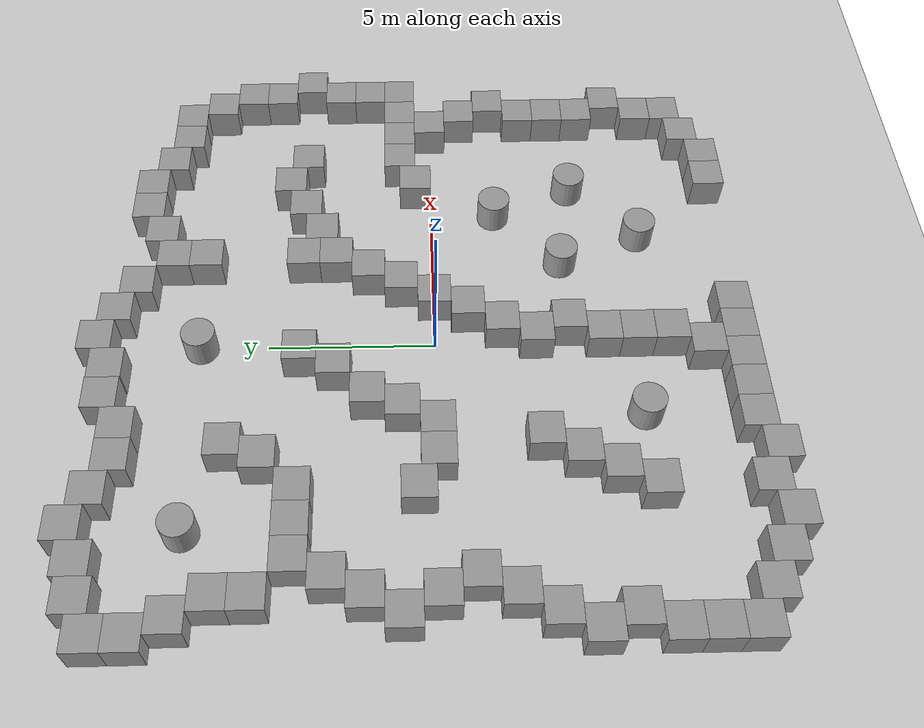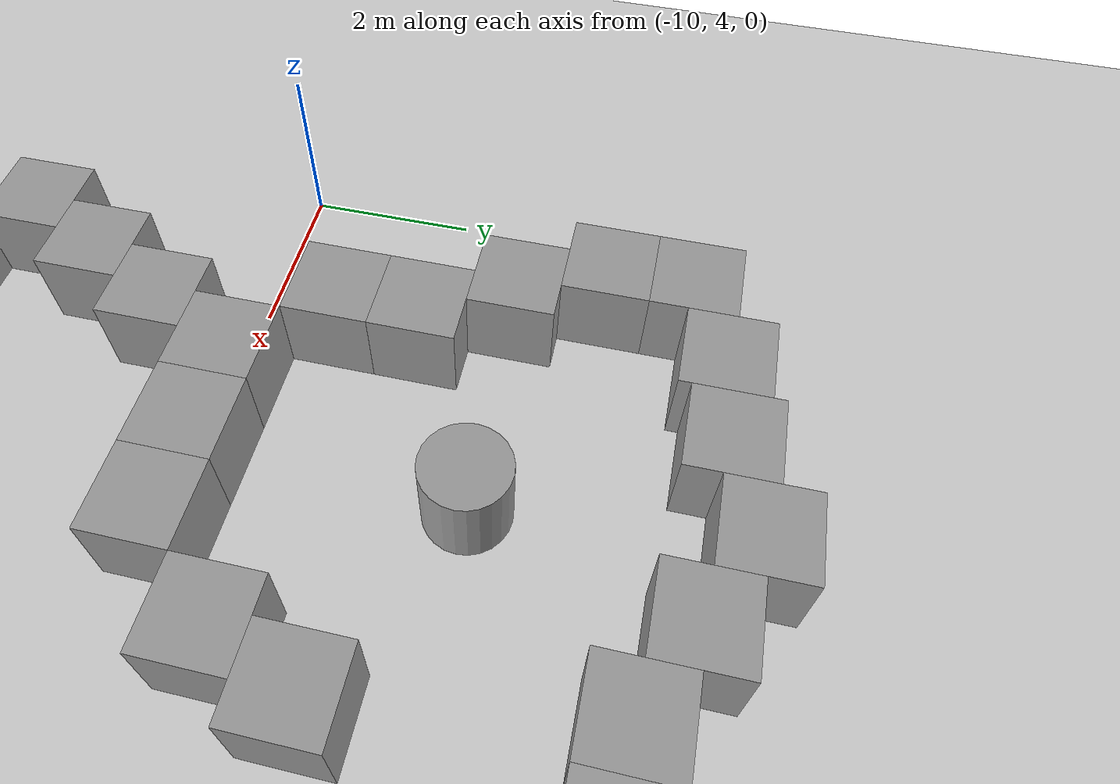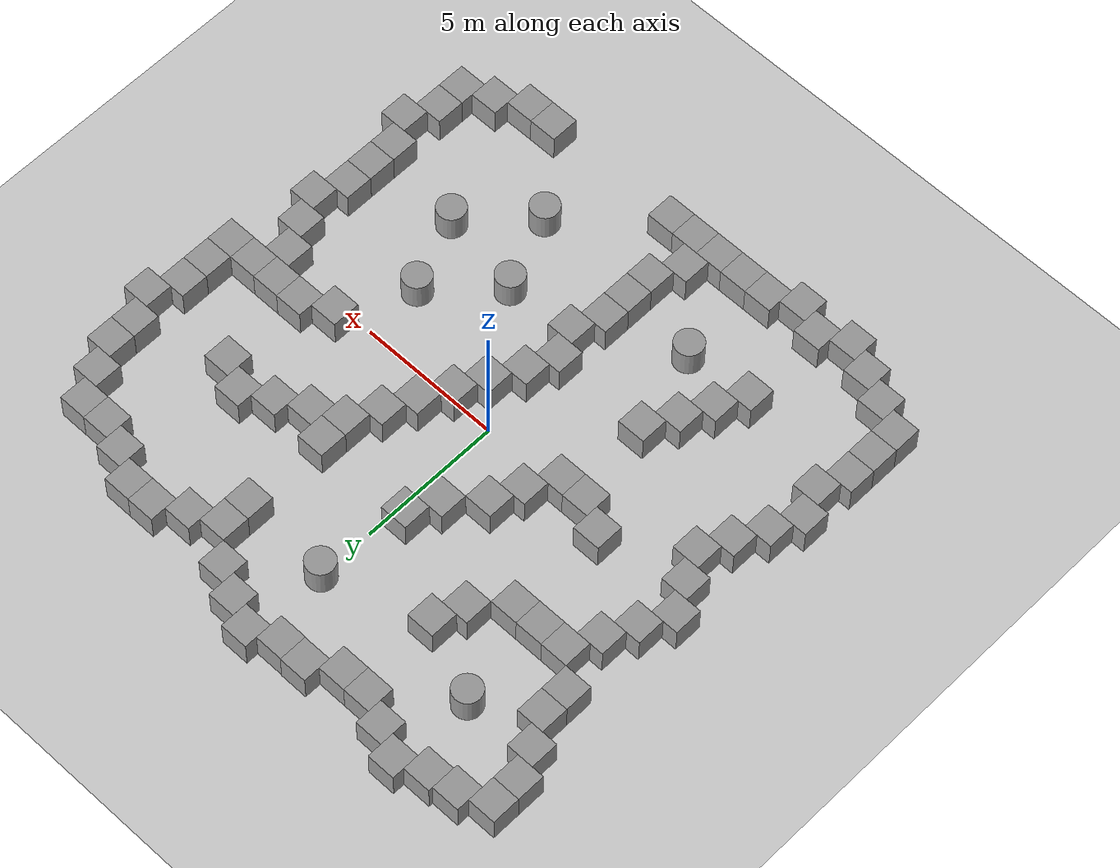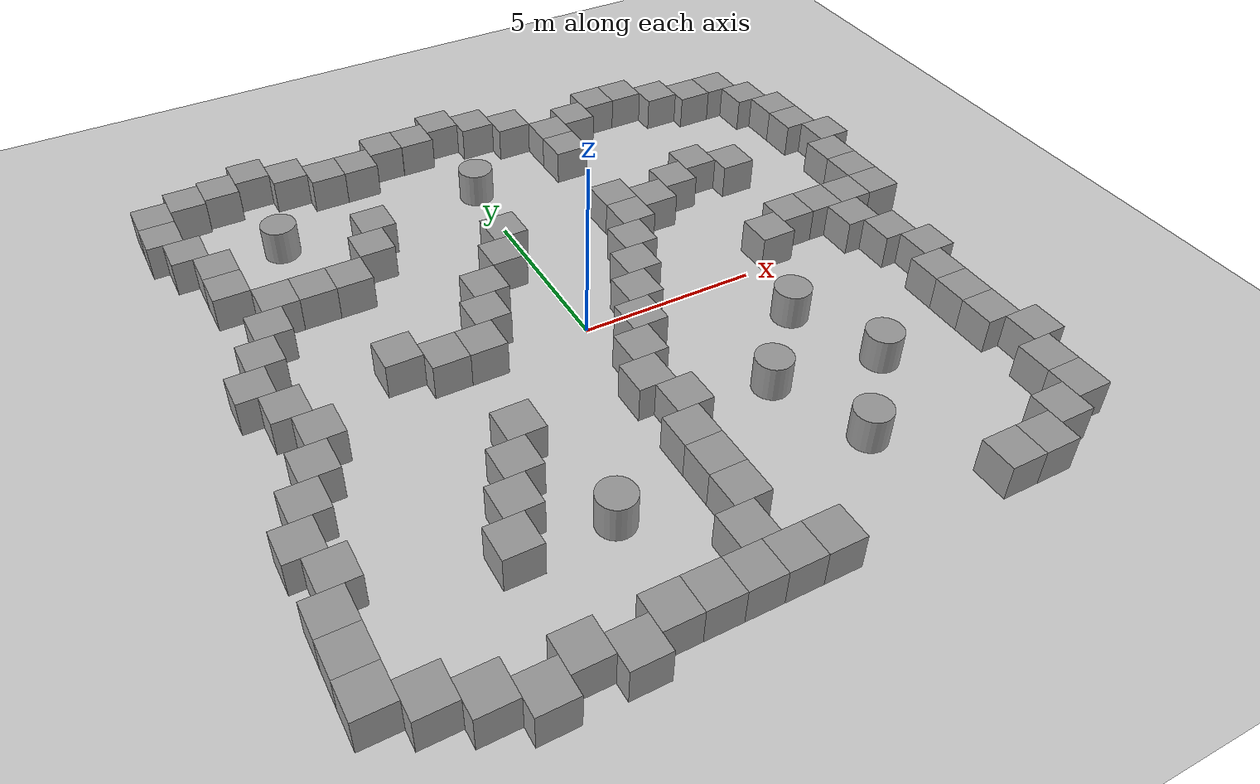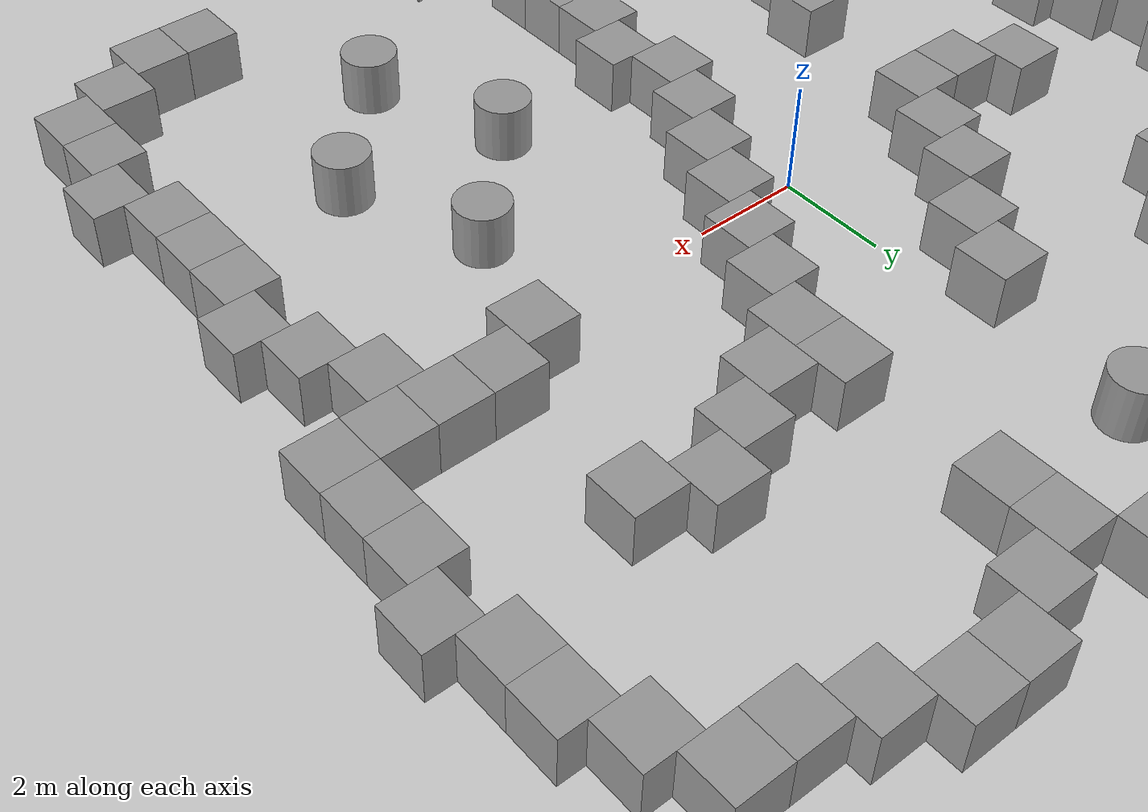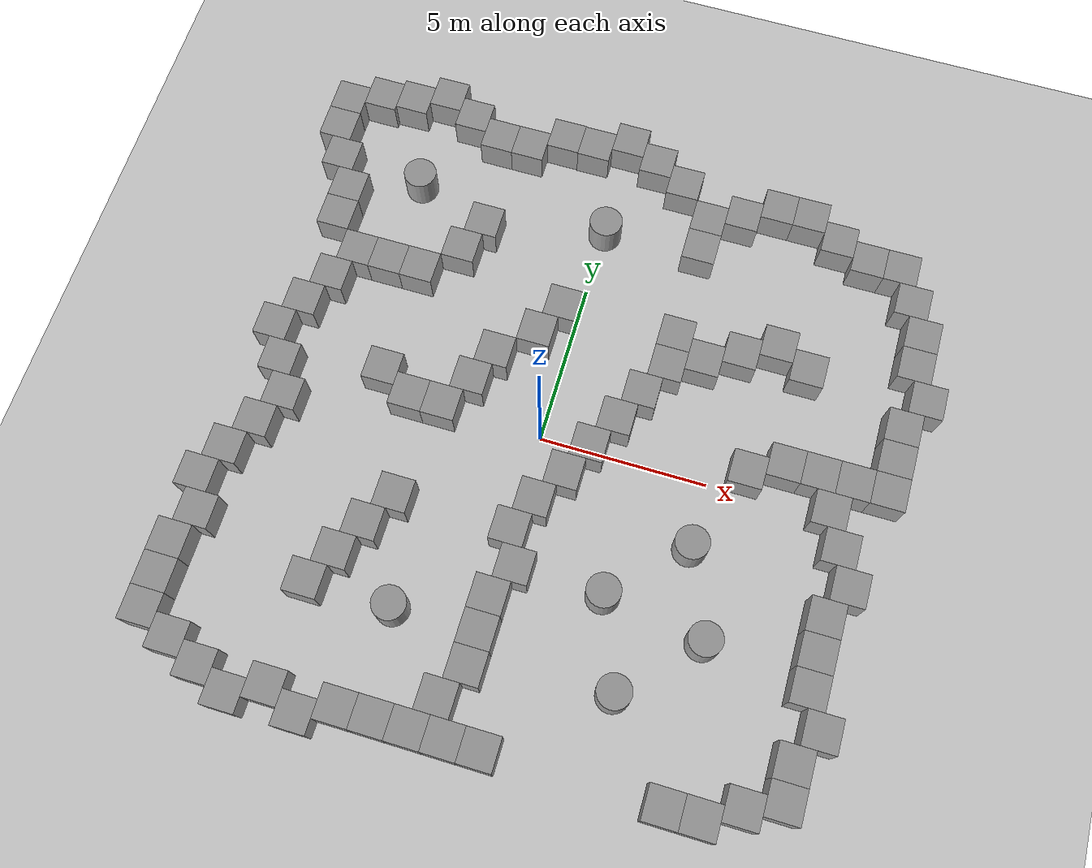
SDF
<sdf version="1.4">
 <world name="default">
  <light name="sun" type="directional">
   <pose>0 0 10 0 -0 0</pose>
   <diffuse>0.8 0.8 0.8 1</diffuse>
   <specular>0.2 0.2 0.2 1</specular>
   <attenuation>
    <range>1000</range>
    <constant>0.9</constant>
    <linear>0.01</linear>
    <quadratic>0.001</quadratic>
   </attenuation>
   <direction>-0.5 0.1 -0.9</direction>
  </light>
  <model name="ground_plane">
   <static>1</static>
   <link name="link">
    <collision name="collision">
     <geometry><plane><normal>0 0 1</normal><size>100 100</size></plane></geometry>
     <surface><friction><ode><mu>100</mu><mu2>50</mu2></ode></friction></surface>
    </collision>
    <visual name="visual">
     <cast_shadows>0</cast_shadows>
     <geometry><plane><normal>0 0 1</normal><size>100 100</size></plane></geometry>
     <material>
      <script><uri>file://media/materials/scripts/gazebo.material</uri><name>Gazebo/Grey</name></script>
     </material>
    </visual>
    <velocity_decay><linear>0</linear><angular>0</angular></velocity_decay>
   </link>
  </model>
  <physics type="ode">
   <max_step_size>0.001</max_step_size>
   <real_time_factor>1</real_time_factor>
   <real_time_update_rate>1000</real_time_update_rate>
   <gravity>0 0 -9.8</gravity>
  </physics>
  <scene><ambient>0.4 0.4 0.4 1</ambient><background>0.7 0.7 0.7 1</background><shadows>1</shadows></scene>
  <spherical_coordinates>
   <surface_model>EARTH_WGS84</surface_model>
   <latitude_deg>0</latitude_deg>
   <longitude_deg>0</longitude_deg>
   <elevation>0</elevation>
   <heading_deg>0</heading_deg>
  </spherical_coordinates>
  <model name="unit_box_1">
   <pose>2e-06 -9 0.5 0 -0 5e-06</pose>
   <link name="link">
    <inertial>
     <mass>1</mass>
     <inertia><ixx>1</ixx><ixy>0</ixy><ixz>0</ixz><iyy>1</iyy><iyz>0</iyz><izz>1</izz></inertia>
    </inertial>
    <collision name="collision"><geometry><box><size>1 1 1</size></box></geometry></collision>
    <visual name="visual">
     <geometry><box><size>1 1 1</size></box></geometry>
     <material>
      <script><uri>file://media/materials/scripts/gazebo.material</uri><name>Gazebo/Grey</name></script>
     </material>
    </visual>
    <velocity_decay><linear>0</linear><angular>0</angular></velocity_decay>
   </link>
   <static>0</static>
  </model>
  <model name="unit_box_2">
   <pose>1.00001 -9 0.5 0 -0 6e-06</pose>
   <link name="link">
    <inertial>
     <mass>1</mass>
     <inertia><ixx>1</ixx><ixy>0</ixy><ixz>0</ixz><iyy>1</iyy><iyz>0</iyz><izz>1</izz></inertia>
    </inertial>
    <collision name="collision"><geometry><box><size>1 1 1</size></box></geometry></collision>
    <visual name="visual">
     <geometry><box><size>1 1 1</size></box></geometry>
     <material>
      <script><uri>file://media/materials/scripts/gazebo.material</uri><name>Gazebo/Grey</name></script>
     </material>
    </visual>
    <velocity_decay><linear>0</linear><angular>0</angular></velocity_decay>
   </link>
   <static>0</static>
  </model>
  <model name="unit_box_3">
   <pose>6 -9 0.5 0 -0 2e-06</pose>
   <link name="link">
    <inertial>
     <mass>1</mass>
     <inertia><ixx>1</ixx><ixy>0</ixy><ixz>0</ixz><iyy>1</iyy><iyz>0</iyz><izz>1</izz></inertia>
    </inertial>
    <collision name="collision"><geometry><box><size>1 1 1</size></box></geometry></collision>
    <visual name="visual">
     <geometry><box><size>1 1 1</size></box></geometry>
     <material>
      <script><uri>file://media/materials/scripts/gazebo.material</uri><name>Gazebo/Grey</name></script>
     </material>
    </visual>
    <velocity_decay><linear>0</linear><angular>0</angular></velocity_decay>
   </link>
   <static>0</static>
  </model>
  <model name="unit_box_4">
   <pose>7 -9 0.5 0 -0 3e-06</pose>
   <link name="link">
    <inertial>
     <mass>1</mass>
     <inertia><ixx>1</ixx><ixy>0</ixy><ixz>0</ixz><iyy>1</iyy><iyz>0</iyz><izz>1</izz></inertia>
    </inertial>
    <collision name="collision"><geometry><box><size>1 1 1</size></box></geometry></collision>
    <visual name="visual">
     <geometry><box><size>1 1 1</size></box></geometry>
     <material>
      <script><uri>file://media/materials/scripts/gazebo.material</uri><name>Gazebo/Grey</name></script>
     </material>
    </visual>
    <velocity_decay><linear>0</linear><angular>0</angular></velocity_decay>
   </link>
   <static>0</static>
  </model>
  <model name="unit_box_5">
   <pose>8 -8.44018 0.5 0 -0 4e-06</pose>
   <link name="link">
    <inertial>
     <mass>1</mass>
     <inertia><ixx>1</ixx><ixy>0</ixy><ixz>0</ixz><iyy>1</iyy><iyz>0</iyz><izz>1</izz></inertia>
    </inertial>
    <collision name="collision"><geometry><box><size>1 1 1</size></box></geometry></collision>
    <visual name="visual">
     <geometry><box><size>1 1 1</size></box></geometry>
     <material>
      <script><uri>file://media/materials/scripts/gazebo.material</uri><name>Gazebo/Grey</name></script>
     </material>
    </visual>
    <velocity_decay><linear>0</linear><angular>0</angular></velocity_decay>
   </link>
   <static>0</static>
  </model>
  <model name="unit_box_6">
   <pose>9 -8.00001 0.5 0 -0 0</pose>
   <link name="link">
    <inertial>
     <mass>1</mass>
     <inertia><ixx>1</ixx><ixy>0</ixy><ixz>0</ixz><iyy>1</iyy><iyz>0</iyz><izz>1</izz></inertia>
    </inertial>
    <collision name="collision"><geometry><box><size>1 1 1</size></box></geometry></collision>
    <visual name="visual">
     <geometry><box><size>1 1 1</size></box></geometry>
     <material>
      <script><uri>file://media/materials/scripts/gazebo.material</uri><name>Gazebo/Grey</name></script>
     </material>
    </visual>
    <velocity_decay><linear>0</linear><angular>0</angular></velocity_decay>
   </link>
   <static>0</static>
  </model>
  <model name="unit_box_7">
   <pose>9 -7 0.5 0 0 -1e-06</pose>
   <link name="link">
    <inertial>
     <mass>1</mass>
     <inertia><ixx>1</ixx><ixy>0</ixy><ixz>0</ixz><iyy>1</iyy><iyz>0</iyz><izz>1</izz></inertia>
    </inertial>
    <collision name="collision"><geometry><box><size>1 1 1</size></box></geometry></collision>
    <visual name="visual">
     <geometry><box><size>1 1 1</size></box></geometry>
     <material>
      <script><uri>file://media/materials/scripts/gazebo.material</uri><name>Gazebo/Grey</name></script>
     </material>
    </visual>
    <velocity_decay><linear>0</linear><angular>0</angular></velocity_decay>
   </link>
   <static>0</static>
  </model>
  <model name="unit_box_8">
   <pose>9.53836 -6 0.5 -0 -0 -1e-06</pose>
   <link name="link">
    <inertial>
     <mass>1</mass>
     <inertia><ixx>1</ixx><ixy>0</ixy><ixz>0</ixz><iyy>1</iyy><iyz>0</iyz><izz>1</izz></inertia>
    </inertial>
    <collision name="collision"><geometry><box><size>1 1 1</size></box></geometry></collision>
    <visual name="visual">
     <geometry><box><size>1 1 1</size></box></geometry>
     <material>
      <script><uri>file://media/materials/scripts/gazebo.material</uri><name>Gazebo/Grey</name></script>
     </material>
    </visual>
    <velocity_decay><linear>0</linear><angular>0</angular></velocity_decay>
   </link>
   <static>0</static>
  </model>
  <model name="unit_box_9">
   <pose>9 -5 0.5 0 -0 0</pose>
   <link name="link">
    <inertial>
     <mass>1</mass>
     <inertia><ixx>1</ixx><ixy>0</ixy><ixz>0</ixz><iyy>1</iyy><iyz>0</iyz><izz>1</izz></inertia>
    </inertial>
    <collision name="collision"><geometry><box><size>1 1 1</size></box></geometry></collision>
    <visual name="visual">
     <geometry><box><size>1 1 1</size></box></geometry>
     <material>
      <script><uri>file://media/materials/scripts/gazebo.material</uri><name>Gazebo/Grey</name></script>
     </material>
    </visual>
    <velocity_decay><linear>0</linear><angular>0</angular></velocity_decay>
   </link>
   <static>0</static>
  </model>
  <model name="unit_box_10">
   <pose>9 -4 0.5 0 -0 1e-06</pose>
   <link name="link">
    <inertial>
     <mass>1</mass>
     <inertia><ixx>1</ixx><ixy>0</ixy><ixz>0</ixz><iyy>1</iyy><iyz>0</iyz><izz>1</izz></inertia>
    </inertial>
    <collision name="collision"><geometry><box><size>1 1 1</size></box></geometry></collision>
    <visual name="visual">
     <geometry><box><size>1 1 1</size></box></geometry>
     <material>
      <script><uri>file://media/materials/scripts/gazebo.material</uri><name>Gazebo/Grey</name></script>
     </material>
    </visual>
    <velocity_decay><linear>0</linear><angular>0</angular></velocity_decay>
   </link>
   <static>0</static>
  </model>
  <model name="unit_box_11">
   <pose>8.99999 -3 0.5 0 -0 2e-06</pose>
   <link name="link">
    <inertial>
     <mass>1</mass>
     <inertia><ixx>1</ixx><ixy>0</ixy><ixz>0</ixz><iyy>1</iyy><iyz>0</iyz><izz>1</izz></inertia>
    </inertial>
    <collision name="collision"><geometry><box><size>1 1 1</size></box></geometry></collision>
    <visual name="visual">
     <geometry><box><size>1 1 1</size></box></geometry>
     <material>
      <script><uri>file://media/materials/scripts/gazebo.material</uri><name>Gazebo/Grey</name></script>
     </material>
    </visual>
    <velocity_decay><linear>0</linear><angular>0</angular></velocity_decay>
   </link>
   <static>0</static>
  </model>
  <model name="unit_box_12">
   <pose>9.4726 -1.99999 0.5 0 -0 1e-05</pose>
   <link name="link">
    <inertial>
     <mass>1</mass>
     <inertia><ixx>1</ixx><ixy>0</ixy><ixz>0</ixz><iyy>1</iyy><iyz>0</iyz><izz>1</izz></inertia>
    </inertial>
    <collision name="collision"><geometry><box><size>1 1 1</size></box></geometry></collision>
    <visual name="visual">
     <geometry><box><size>1 1 1</size></box></geometry>
     <material>
      <script><uri>file://media/materials/scripts/gazebo.material</uri><name>Gazebo/Grey</name></script>
     </material>
    </visual>
    <velocity_decay><linear>0</linear><angular>0</angular></velocity_decay>
   </link>
   <static>0</static>
  </model>
  <model name="unit_box_13">
   <pose>9 -0.999999 0.5 0 -0 1.1e-05</pose>
   <link name="link">
    <inertial>
     <mass>1</mass>
     <inertia><ixx>1</ixx><ixy>0</ixy><ixz>0</ixz><iyy>1</iyy><iyz>0</iyz><izz>1</izz></inertia>
    </inertial>
    <collision name="collision"><geometry><box><size>1 1 1</size></box></geometry></collision>
    <visual name="visual">
     <geometry><box><size>1 1 1</size></box></geometry>
     <material>
      <script><uri>file://media/materials/scripts/gazebo.material</uri><name>Gazebo/Grey</name></script>
     </material>
    </visual>
    <velocity_decay><linear>0</linear><angular>0</angular></velocity_decay>
   </link>
   <static>0</static>
  </model>
  <model name="unit_box_14">
   <pose>8.50667 -1e-06 0.5 0 -0 4e-06</pose>
   <link name="link">
    <inertial>
     <mass>1</mass>
     <inertia><ixx>1</ixx><ixy>0</ixy><ixz>0</ixz><iyy>1</iyy><iyz>0</iyz><izz>1</izz></inertia>
    </inertial>
    <collision name="collision"><geometry><box><size>1 1 1</size></box></geometry></collision>
    <visual name="visual">
     <geometry><box><size>1 1 1</size></box></geometry>
     <material>
      <script><uri>file://media/materials/scripts/gazebo.material</uri><name>Gazebo/Grey</name></script>
     </material>
    </visual>
    <velocity_decay><linear>0</linear><angular>0</angular></velocity_decay>
   </link>
   <static>0</static>
  </model>
  <model name="unit_box_15">
   <pose>8 0.999998 0.5 0 -0 6e-06</pose>
   <link name="link">
    <inertial>
     <mass>1</mass>
     <inertia><ixx>1</ixx><ixy>0</ixy><ixz>0</ixz><iyy>1</iyy><iyz>0</iyz><izz>1</izz></inertia>
    </inertial>
    <collision name="collision"><geometry><box><size>1 1 1</size></box></geometry></collision>
    <visual name="visual">
     <geometry><box><size>1 1 1</size></box></geometry>
     <material>
      <script><uri>file://media/materials/scripts/gazebo.material</uri><name>Gazebo/Grey</name></script>
     </material>
    </visual>
    <velocity_decay><linear>0</linear><angular>0</angular></velocity_decay>
   </link>
   <static>0</static>
  </model>
  <model name="unit_box_16">
   <pose>-0.505545 -8 0.5 0 -0 3e-06</pose>
   <link name="link">
    <inertial>
     <mass>1</mass>
     <inertia><ixx>1</ixx><ixy>0</ixy><ixz>0</ixz><iyy>1</iyy><iyz>0</iyz><izz>1</izz></inertia>
    </inertial>
    <collision name="collision"><geometry><box><size>1 1 1</size></box></geometry></collision>
    <visual name="visual">
     <geometry><box><size>1 1 1</size></box></geometry>
     <material>
      <script><uri>file://media/materials/scripts/gazebo.material</uri><name>Gazebo/Grey</name></script>
     </material>
    </visual>
    <velocity_decay><linear>0</linear><angular>0</angular></velocity_decay>
   </link>
   <static>0</static>
  </model>
  <model name="unit_box_17">
   <pose>1e-06 -7 0.5 0 0 -3e-06</pose>
   <link name="link">
    <inertial>
     <mass>1</mass>
     <inertia><ixx>1</ixx><ixy>0</ixy><ixz>0</ixz><iyy>1</iyy><iyz>0</iyz><izz>1</izz></inertia>
    </inertial>
    <collision name="collision"><geometry><box><size>1 1 1</size></box></geometry></collision>
    <visual name="visual">
     <geometry><box><size>1 1 1</size></box></geometry>
     <material>
      <script><uri>file://media/materials/scripts/gazebo.material</uri><name>Gazebo/Grey</name></script>
     </material>
    </visual>
    <velocity_decay><linear>0</linear><angular>0</angular></velocity_decay>
   </link>
   <static>0</static>
  </model>
  <model name="unit_box_18">
   <pose>9e-06 -6 0.5 0 -0 -3e-06</pose>
   <link name="link">
    <inertial>
     <mass>1</mass>
     <inertia><ixx>1</ixx><ixy>0</ixy><ixz>0</ixz><iyy>1</iyy><iyz>0</iyz><izz>1</izz></inertia>
    </inertial>
    <collision name="collision"><geometry><box><size>1 1 1</size></box></geometry></collision>
    <visual name="visual">
     <geometry><box><size>1 1 1</size></box></geometry>
     <material>
      <script><uri>file://media/materials/scripts/gazebo.material</uri><name>Gazebo/Grey</name></script>
     </material>
    </visual>
    <velocity_decay><linear>0</linear><angular>0</angular></velocity_decay>
   </link>
   <static>0</static>
  </model>
  <model name="unit_box_19">
   <pose>1.6e-05 -5 0.5 0 0 -3e-06</pose>
   <link name="link">
    <inertial>
     <mass>1</mass>
     <inertia><ixx>1</ixx><ixy>0</ixy><ixz>0</ixz><iyy>1</iyy><iyz>0</iyz><izz>1</izz></inertia>
    </inertial>
    <collision name="collision"><geometry><box><size>1 1 1</size></box></geometry></collision>
    <visual name="visual">
     <geometry><box><size>1 1 1</size></box></geometry>
     <material>
      <script><uri>file://media/materials/scripts/gazebo.material</uri><name>Gazebo/Grey</name></script>
     </material>
    </visual>
    <velocity_decay><linear>0</linear><angular>0</angular></velocity_decay>
   </link>
   <static>0</static>
  </model>
  <model name="unit_box_20">
   <pose>0.438754 -4 0.5 0 0 -3e-06</pose>
   <link name="link">
    <inertial>
     <mass>1</mass>
     <inertia><ixx>1</ixx><ixy>0</ixy><ixz>0</ixz><iyy>1</iyy><iyz>0</iyz><izz>1</izz></inertia>
    </inertial>
    <collision name="collision"><geometry><box><size>1 1 1</size></box></geometry></collision>
    <visual name="visual">
     <geometry><box><size>1 1 1</size></box></geometry>
     <material>
      <script><uri>file://media/materials/scripts/gazebo.material</uri><name>Gazebo/Grey</name></script>
     </material>
    </visual>
    <velocity_decay><linear>0</linear><angular>0</angular></velocity_decay>
   </link>
   <static>0</static>
  </model>
  <model name="unit_box_21">
   <pose>1.6e-05 -3 0.5 0 0 -6e-06</pose>
   <link name="link">
    <inertial>
     <mass>1</mass>
     <inertia><ixx>1</ixx><ixy>0</ixy><ixz>0</ixz><iyy>1</iyy><iyz>0</iyz><izz>1</izz></inertia>
    </inertial>
    <collision name="collision"><geometry><box><size>1 1 1</size></box></geometry></collision>
    <visual name="visual">
     <geometry><box><size>1 1 1</size></box></geometry>
     <material>
      <script><uri>file://media/materials/scripts/gazebo.material</uri><name>Gazebo/Grey</name></script>
     </material>
    </visual>
    <velocity_decay><linear>0</linear><angular>0</angular></velocity_decay>
   </link>
   <static>0</static>
  </model>
  <model name="unit_box_22">
   <pose>0.407129 -2 0.5 -0 -0 -8e-06</pose>
   <link name="link">
    <inertial>
     <mass>1</mass>
     <inertia><ixx>1</ixx><ixy>0</ixy><ixz>0</ixz><iyy>1</iyy><iyz>0</iyz><izz>1</izz></inertia>
    </inertial>
    <collision name="collision"><geometry><box><size>1 1 1</size></box></geometry></collision>
    <visual name="visual">
     <geometry><box><size>1 1 1</size></box></geometry>
     <material>
      <script><uri>file://media/materials/scripts/gazebo.material</uri><name>Gazebo/Grey</name></script>
     </material>
    </visual>
    <velocity_decay><linear>0</linear><angular>0</angular></velocity_decay>
   </link>
   <static>0</static>
  </model>
  <model name="unit_box_23">
   <pose>1 -1 0.5 0 0 -4e-06</pose>
   <link name="link">
    <inertial>
     <mass>1</mass>
     <inertia><ixx>1</ixx><ixy>0</ixy><ixz>0</ixz><iyy>1</iyy><iyz>0</iyz><izz>1</izz></inertia>
    </inertial>
    <collision name="collision"><geometry><box><size>1 1 1</size></box></geometry></collision>
    <visual name="visual">
     <geometry><box><size>1 1 1</size></box></geometry>
     <material>
      <script><uri>file://media/materials/scripts/gazebo.material</uri><name>Gazebo/Grey</name></script>
     </material>
    </visual>
    <velocity_decay><linear>0</linear><angular>0</angular></velocity_decay>
   </link>
   <static>0</static>
  </model>
  <model name="unit_box_24">
   <pose>1.46387 5e-06 0.5 -0 -0 -8e-06</pose>
   <link name="link">
    <inertial>
     <mass>1</mass>
     <inertia><ixx>1</ixx><ixy>0</ixy><ixz>0</ixz><iyy>1</iyy><iyz>0</iyz><izz>1</izz></inertia>
    </inertial>
    <collision name="collision"><geometry><box><size>1 1 1</size></box></geometry></collision>
    <visual name="visual">
     <geometry><box><size>1 1 1</size></box></geometry>
     <material>
      <script><uri>file://media/materials/scripts/gazebo.material</uri><name>Gazebo/Grey</name></script>
     </material>
    </visual>
    <velocity_decay><linear>0</linear><angular>0</angular></velocity_decay>
   </link>
   <static>0</static>
  </model>
  <model name="unit_box_25">
   <pose>2 1 0.5 -0 -0 -8e-06</pose>
   <link name="link">
    <inertial>
     <mass>1</mass>
     <inertia><ixx>1</ixx><ixy>0</ixy><ixz>0</ixz><iyy>1</iyy><iyz>0</iyz><izz>1</izz></inertia>
    </inertial>
    <collision name="collision"><geometry><box><size>1 1 1</size></box></geometry></collision>
    <visual name="visual">
     <geometry><box><size>1 1 1</size></box></geometry>
     <material>
      <script><uri>file://media/materials/scripts/gazebo.material</uri><name>Gazebo/Grey</name></script>
     </material>
    </visual>
    <velocity_decay><linear>0</linear><angular>0</angular></velocity_decay>
   </link>
   <static>0</static>
  </model>
  <model name="unit_box_26">
   <pose>2.48015 2 0.5 -0 -0 -7e-06</pose>
   <link name="link">
    <inertial>
     <mass>1</mass>
     <inertia><ixx>1</ixx><ixy>0</ixy><ixz>0</ixz><iyy>1</iyy><iyz>0</iyz><izz>1</izz></inertia>
    </inertial>
    <collision name="collision"><geometry><box><size>1 1 1</size></box></geometry></collision>
    <visual name="visual">
     <geometry><box><size>1 1 1</size></box></geometry>
     <material>
      <script><uri>file://media/materials/scripts/gazebo.material</uri><name>Gazebo/Grey</name></script>
     </material>
    </visual>
    <velocity_decay><linear>0</linear><angular>0</angular></velocity_decay>
   </link>
   <static>0</static>
  </model>
  <model name="unit_box_27">
   <pose>3 3 0.5 0 0 -4e-06</pose>
   <link name="link">
    <inertial>
     <mass>1</mass>
     <inertia><ixx>1</ixx><ixy>0</ixy><ixz>0</ixz><iyy>1</iyy><iyz>0</iyz><izz>1</izz></inertia>
    </inertial>
    <collision name="collision"><geometry><box><size>1 1 1</size></box></geometry></collision>
    <visual name="visual">
     <geometry><box><size>1 1 1</size></box></geometry>
     <material>
      <script><uri>file://media/materials/scripts/gazebo.material</uri><name>Gazebo/Grey</name></script>
     </material>
    </visual>
    <velocity_decay><linear>0</linear><angular>0</angular></velocity_decay>
   </link>
   <static>0</static>
  </model>
  <model name="unit_box_28">
   <pose>3 4 0.5 -0 -0 -3e-06</pose>
   <link name="link">
    <inertial>
     <mass>1</mass>
     <inertia><ixx>1</ixx><ixy>0</ixy><ixz>0</ixz><iyy>1</iyy><iyz>0</iyz><izz>1</izz></inertia>
    </inertial>
    <collision name="collision"><geometry><box><size>1 1 1</size></box></geometry></collision>
    <visual name="visual">
     <geometry><box><size>1 1 1</size></box></geometry>
     <material>
      <script><uri>file://media/materials/scripts/gazebo.material</uri><name>Gazebo/Grey</name></script>
     </material>
    </visual>
    <velocity_decay><linear>0</linear><angular>0</angular></velocity_decay>
   </link>
   <static>0</static>
  </model>
  <model name="unit_box_29">
   <pose>3 7 0.5 0 -0 1.3e-05</pose>
   <link name="link">
    <inertial>
     <mass>1</mass>
     <inertia><ixx>1</ixx><ixy>0</ixy><ixz>0</ixz><iyy>1</iyy><iyz>0</iyz><izz>1</izz></inertia>
    </inertial>
    <collision name="collision"><geometry><box><size>1 1 1</size></box></geometry></collision>
    <visual name="visual">
     <geometry><box><size>1 1 1</size></box></geometry>
     <material>
      <script><uri>file://media/materials/scripts/gazebo.material</uri><name>Gazebo/Grey</name></script>
     </material>
    </visual>
    <velocity_decay><linear>0</linear><angular>0</angular></velocity_decay>
   </link>
   <static>0</static>
  </model>
  <model name="unit_box_30">
   <pose>4 3.46526 0.5 0 -0 -3e-06</pose>
   <link name="link">
    <inertial>
     <mass>1</mass>
     <inertia><ixx>1</ixx><ixy>0</ixy><ixz>0</ixz><iyy>1</iyy><iyz>0</iyz><izz>1</izz></inertia>
    </inertial>
    <collision name="collision"><geometry><box><size>1 1 1</size></box></geometry></collision>
    <visual name="visual">
     <geometry><box><size>1 1 1</size></box></geometry>
     <material>
      <script><uri>file://media/materials/scripts/gazebo.material</uri><name>Gazebo/Grey</name></script>
     </material>
    </visual>
    <velocity_decay><linear>0</linear><angular>0</angular></velocity_decay>
   </link>
   <static>0</static>
  </model>
  <model name="unit_box_31">
   <pose>5 4 0.5 0 -0 9e-06</pose>
   <link name="link">
    <inertial>
     <mass>1</mass>
     <inertia><ixx>1</ixx><ixy>0</ixy><ixz>0</ixz><iyy>1</iyy><iyz>0</iyz><izz>1</izz></inertia>
    </inertial>
    <collision name="collision"><geometry><box><size>1 1 1</size></box></geometry></collision>
    <visual name="visual">
     <geometry><box><size>1 1 1</size></box></geometry>
     <material>
      <script><uri>file://media/materials/scripts/gazebo.material</uri><name>Gazebo/Grey</name></script>
     </material>
    </visual>
    <velocity_decay><linear>0</linear><angular>0</angular></velocity_decay>
   </link>
   <static>0</static>
  </model>
  <model name="unit_box_32">
   <pose>6 4.53052 0.5 0 -0 7e-06</pose>
   <link name="link">
    <inertial>
     <mass>1</mass>
     <inertia><ixx>1</ixx><ixy>0</ixy><ixz>0</ixz><iyy>1</iyy><iyz>0</iyz><izz>1</izz></inertia>
    </inertial>
    <collision name="collision"><geometry><box><size>1 1 1</size></box></geometry></collision>
    <visual name="visual">
     <geometry><box><size>1 1 1</size></box></geometry>
     <material>
      <script><uri>file://media/materials/scripts/gazebo.material</uri><name>Gazebo/Grey</name></script>
     </material>
    </visual>
    <velocity_decay><linear>0</linear><angular>0</angular></velocity_decay>
   </link>
   <static>0</static>
  </model>
  <model name="unit_box_33">
   <pose>7 1 0.5 0 -0 2e-06</pose>
   <link name="link">
    <inertial>
     <mass>1</mass>
     <inertia><ixx>1</ixx><ixy>0</ixy><ixz>0</ixz><iyy>1</iyy><iyz>0</iyz><izz>1</izz></inertia>
    </inertial>
    <collision name="collision"><geometry><box><size>1 1 1</size></box></geometry></collision>
    <visual name="visual">
     <geometry><box><size>1 1 1</size></box></geometry>
     <material>
      <script><uri>file://media/materials/scripts/gazebo.material</uri><name>Gazebo/Grey</name></script>
     </material>
    </visual>
    <velocity_decay><linear>0</linear><angular>0</angular></velocity_decay>
   </link>
   <static>0</static>
  </model>
  <model name="unit_box_34">
   <pose>6 0.509657 0.5 0 -0 2e-06</pose>
   <link name="link">
    <inertial>
     <mass>1</mass>
     <inertia><ixx>1</ixx><ixy>0</ixy><ixz>0</ixz><iyy>1</iyy><iyz>0</iyz><izz>1</izz></inertia>
    </inertial>
    <collision name="collision"><geometry><box><size>1 1 1</size></box></geometry></collision>
    <visual name="visual">
     <geometry><box><size>1 1 1</size></box></geometry>
     <material>
      <script><uri>file://media/materials/scripts/gazebo.material</uri><name>Gazebo/Grey</name></script>
     </material>
    </visual>
    <velocity_decay><linear>0</linear><angular>0</angular></velocity_decay>
   </link>
   <static>0</static>
  </model>
  <model name="unit_box_35">
   <pose>7 4 0.5 0 -0 3e-06</pose>
   <link name="link">
    <inertial>
     <mass>1</mass>
     <inertia><ixx>1</ixx><ixy>0</ixy><ixz>0</ixz><iyy>1</iyy><iyz>0</iyz><izz>1</izz></inertia>
    </inertial>
    <collision name="collision"><geometry><box><size>1 1 1</size></box></geometry></collision>
    <visual name="visual">
     <geometry><box><size>1 1 1</size></box></geometry>
     <material>
      <script><uri>file://media/materials/scripts/gazebo.material</uri><name>Gazebo/Grey</name></script>
     </material>
    </visual>
    <velocity_decay><linear>0</linear><angular>0</angular></velocity_decay>
   </link>
   <static>0</static>
  </model>
  <model name="unit_box_36">
   <pose>9.00001 1 0.5 0 0 -8e-06</pose>
   <link name="link">
    <inertial>
     <mass>1</mass>
     <inertia><ixx>1</ixx><ixy>0</ixy><ixz>0</ixz><iyy>1</iyy><iyz>0</iyz><izz>1</izz></inertia>
    </inertial>
    <collision name="collision"><geometry><box><size>1 1 1</size></box></geometry></collision>
    <visual name="visual">
     <geometry><box><size>1 1 1</size></box></geometry>
     <material>
      <script><uri>file://media/materials/scripts/gazebo.material</uri><name>Gazebo/Grey</name></script>
     </material>
    </visual>
    <velocity_decay><linear>0</linear><angular>0</angular></velocity_decay>
   </link>
   <static>0</static>
  </model>
  <model name="unit_box_37">
   <pose>10 0.999997 0.5 -1e-06 1e-06 -9e-06</pose>
   <link name="link">
    <inertial>
     <mass>1</mass>
     <inertia><ixx>1</ixx><ixy>0</ixy><ixz>0</ixz><iyy>1</iyy><iyz>0</iyz><izz>1</izz></inertia>
    </inertial>
    <collision name="collision"><geometry><box><size>1 1 1</size></box></geometry></collision>
    <visual name="visual">
     <geometry><box><size>1 1 1</size></box></geometry>
     <material>
      <script><uri>file://media/materials/scripts/gazebo.material</uri><name>Gazebo/Grey</name></script>
     </material>
    </visual>
    <velocity_decay><linear>0</linear><angular>0</angular></velocity_decay>
   </link>
   <static>0</static>
  </model>
  <model name="unit_box_38">
   <pose>10 2 0.5 -0 -0 -9e-06</pose>
   <link name="link">
    <inertial>
     <mass>1</mass>
     <inertia><ixx>1</ixx><ixy>0</ixy><ixz>0</ixz><iyy>1</iyy><iyz>0</iyz><izz>1</izz></inertia>
    </inertial>
    <collision name="collision"><geometry><box><size>1 1 1</size></box></geometry></collision>
    <visual name="visual">
     <geometry><box><size>1 1 1</size></box></geometry>
     <material>
      <script><uri>file://media/materials/scripts/gazebo.material</uri><name>Gazebo/Grey</name></script>
     </material>
    </visual>
    <velocity_decay><linear>0</linear><angular>0</angular></velocity_decay>
   </link>
   <static>0</static>
  </model>
  <model name="unit_box_39">
   <pose>10 3 0.5 -0 -0 -1e-05</pose>
   <link name="link">
    <inertial>
     <mass>1</mass>
     <inertia><ixx>1</ixx><ixy>0</ixy><ixz>0</ixz><iyy>1</iyy><iyz>0</iyz><izz>1</izz></inertia>
    </inertial>
    <collision name="collision"><geometry><box><size>1 1 1</size></box></geometry></collision>
    <visual name="visual">
     <geometry><box><size>1 1 1</size></box></geometry>
     <material>
      <script><uri>file://media/materials/scripts/gazebo.material</uri><name>Gazebo/Grey</name></script>
     </material>
    </visual>
    <velocity_decay><linear>0</linear><angular>0</angular></velocity_decay>
   </link>
   <static>0</static>
  </model>
  <model name="unit_box_40">
   <pose>10.5198 4 0.5 0 -0 5e-06</pose>
   <link name="link">
    <inertial>
     <mass>1</mass>
     <inertia><ixx>1</ixx><ixy>0</ixy><ixz>0</ixz><iyy>1</iyy><iyz>0</iyz><izz>1</izz></inertia>
    </inertial>
    <collision name="collision"><geometry><box><size>1 1 1</size></box></geometry></collision>
    <visual name="visual">
     <geometry><box><size>1 1 1</size></box></geometry>
     <material>
      <script><uri>file://media/materials/scripts/gazebo.material</uri><name>Gazebo/Grey</name></script>
     </material>
    </visual>
    <velocity_decay><linear>0</linear><angular>0</angular></velocity_decay>
   </link>
   <static>0</static>
  </model>
  <model name="unit_box_41">
   <pose>10 5 0.5 0 -0 8e-06</pose>
   <link name="link">
    <inertial>
     <mass>1</mass>
     <inertia><ixx>1</ixx><ixy>0</ixy><ixz>0</ixz><iyy>1</iyy><iyz>0</iyz><izz>1</izz></inertia>
    </inertial>
    <collision name="collision"><geometry><box><size>1 1 1</size></box></geometry></collision>
    <visual name="visual">
     <geometry><box><size>1 1 1</size></box></geometry>
     <material>
      <script><uri>file://media/materials/scripts/gazebo.material</uri><name>Gazebo/Grey</name></script>
     </material>
    </visual>
    <velocity_decay><linear>0</linear><angular>0</angular></velocity_decay>
   </link>
   <static>0</static>
  </model>
  <model name="unit_box_42">
   <pose>10 6 0.5 0 -0 8e-06</pose>
   <link name="link">
    <inertial>
     <mass>1</mass>
     <inertia><ixx>1</ixx><ixy>0</ixy><ixz>0</ixz><iyy>1</iyy><iyz>0</iyz><izz>1</izz></inertia>
    </inertial>
    <collision name="collision"><geometry><box><size>1 1 1</size></box></geometry></collision>
    <visual name="visual">
     <geometry><box><size>1 1 1</size></box></geometry>
     <material>
      <script><uri>file://media/materials/scripts/gazebo.material</uri><name>Gazebo/Grey</name></script>
     </material>
    </visual>
    <velocity_decay><linear>0</linear><angular>0</angular></velocity_decay>
   </link>
   <static>0</static>
  </model>
  <model name="unit_box_43">
   <pose>9.52562 7 0.5 0 -0 3e-06</pose>
   <link name="link">
    <inertial>
     <mass>1</mass>
     <inertia><ixx>1</ixx><ixy>0</ixy><ixz>0</ixz><iyy>1</iyy><iyz>0</iyz><izz>1</izz></inertia>
    </inertial>
    <collision name="collision"><geometry><box><size>1 1 1</size></box></geometry></collision>
    <visual name="visual">
     <geometry><box><size>1 1 1</size></box></geometry>
     <material>
      <script><uri>file://media/materials/scripts/gazebo.material</uri><name>Gazebo/Grey</name></script>
     </material>
    </visual>
    <velocity_decay><linear>0</linear><angular>0</angular></velocity_decay>
   </link>
   <static>0</static>
  </model>
  <model name="unit_box_44">
   <pose>9 8.00001 0.5 0 -0 -4e-06</pose>
   <link name="link">
    <inertial>
     <mass>1</mass>
     <inertia><ixx>1</ixx><ixy>0</ixy><ixz>0</ixz><iyy>1</iyy><iyz>0</iyz><izz>1</izz></inertia>
    </inertial>
    <collision name="collision"><geometry><box><size>1 1 1</size></box></geometry></collision>
    <visual name="visual">
     <geometry><box><size>1 1 1</size></box></geometry>
     <material>
      <script><uri>file://media/materials/scripts/gazebo.material</uri><name>Gazebo/Grey</name></script>
     </material>
    </visual>
    <velocity_decay><linear>0</linear><angular>0</angular></velocity_decay>
   </link>
   <static>0</static>
  </model>
  <model name="unit_box_45">
   <pose>8 8 0.5 0 -0 -4e-06</pose>
   <link name="link">
    <inertial>
     <mass>1</mass>
     <inertia><ixx>1</ixx><ixy>0</ixy><ixz>0</ixz><iyy>1</iyy><iyz>0</iyz><izz>1</izz></inertia>
    </inertial>
    <collision name="collision"><geometry><box><size>1 1 1</size></box></geometry></collision>
    <visual name="visual">
     <geometry><box><size>1 1 1</size></box></geometry>
     <material>
      <script><uri>file://media/materials/scripts/gazebo.material</uri><name>Gazebo/Grey</name></script>
     </material>
    </visual>
    <velocity_decay><linear>0</linear><angular>0</angular></velocity_decay>
   </link>
   <static>0</static>
  </model>
  <model name="unit_box_46">
   <pose>7 8.40883 0.5 0 0 -1e-05</pose>
   <link name="link">
    <inertial>
     <mass>1</mass>
     <inertia><ixx>1</ixx><ixy>0</ixy><ixz>0</ixz><iyy>1</iyy><iyz>0</iyz><izz>1</izz></inertia>
    </inertial>
    <collision name="collision"><geometry><box><size>1 1 1</size></box></geometry></collision>
    <visual name="visual">
     <geometry><box><size>1 1 1</size></box></geometry>
     <material>
      <script><uri>file://media/materials/scripts/gazebo.material</uri><name>Gazebo/Grey</name></script>
     </material>
    </visual>
    <velocity_decay><linear>0</linear><angular>0</angular></velocity_decay>
   </link>
   <static>0</static>
  </model>
  <model name="unit_box_47">
   <pose>6 8.99999 0.5 0 -0 6e-06</pose>
   <link name="link">
    <inertial>
     <mass>1</mass>
     <inertia><ixx>1</ixx><ixy>0</ixy><ixz>0</ixz><iyy>1</iyy><iyz>0</iyz><izz>1</izz></inertia>
    </inertial>
    <collision name="collision"><geometry><box><size>1 1 1</size></box></geometry></collision>
    <visual name="visual">
     <geometry><box><size>1 1 1</size></box></geometry>
     <material>
      <script><uri>file://media/materials/scripts/gazebo.material</uri><name>Gazebo/Grey</name></script>
     </material>
    </visual>
    <velocity_decay><linear>0</linear><angular>0</angular></velocity_decay>
   </link>
   <static>0</static>
  </model>
  <model name="unit_box_48">
   <pose>5 8.99998 0.5 0 -0 6e-06</pose>
   <link name="link">
    <inertial>
     <mass>1</mass>
     <inertia><ixx>1</ixx><ixy>0</ixy><ixz>0</ixz><iyy>1</iyy><iyz>0</iyz><izz>1</izz></inertia>
    </inertial>
    <collision name="collision"><geometry><box><size>1 1 1</size></box></geometry></collision>
    <visual name="visual">
     <geometry><box><size>1 1 1</size></box></geometry>
     <material>
      <script><uri>file://media/materials/scripts/gazebo.material</uri><name>Gazebo/Grey</name></script>
     </material>
    </visual>
    <velocity_decay><linear>0</linear><angular>0</angular></velocity_decay>
   </link>
   <static>0</static>
  </model>
  <model name="unit_box_49">
   <pose>4 8.45386 0.5 0 -0 9e-06</pose>
   <link name="link">
    <inertial>
     <mass>1</mass>
     <inertia><ixx>1</ixx><ixy>0</ixy><ixz>0</ixz><iyy>1</iyy><iyz>0</iyz><izz>1</izz></inertia>
    </inertial>
    <collision name="collision"><geometry><box><size>1 1 1</size></box></geometry></collision>
    <visual name="visual">
     <geometry><box><size>1 1 1</size></box></geometry>
     <material>
      <script><uri>file://media/materials/scripts/gazebo.material</uri><name>Gazebo/Grey</name></script>
     </material>
    </visual>
    <velocity_decay><linear>0</linear><angular>0</angular></velocity_decay>
   </link>
   <static>0</static>
  </model>
  <model name="unit_box_50">
   <pose>3 8.00001 0.5 0 -0 1.7e-05</pose>
   <link name="link">
    <inertial>
     <mass>1</mass>
     <inertia><ixx>1</ixx><ixy>0</ixy><ixz>0</ixz><iyy>1</iyy><iyz>0</iyz><izz>1</izz></inertia>
    </inertial>
    <collision name="collision"><geometry><box><size>1 1 1</size></box></geometry></collision>
    <visual name="visual">
     <geometry><box><size>1 1 1</size></box></geometry>
     <material>
      <script><uri>file://media/materials/scripts/gazebo.material</uri><name>Gazebo/Grey</name></script>
     </material>
    </visual>
    <velocity_decay><linear>0</linear><angular>0</angular></velocity_decay>
   </link>
   <static>0</static>
  </model>
  <model name="unit_box_51">
   <pose>-0.493767 4 0.5 0 -0 0</pose>
   <link name="link">
    <inertial>
     <mass>1</mass>
     <inertia><ixx>1</ixx><ixy>0</ixy><ixz>0</ixz><iyy>1</iyy><iyz>0</iyz><izz>1</izz></inertia>
    </inertial>
    <collision name="collision"><geometry><box><size>1 1 1</size></box></geometry></collision>
    <visual name="visual">
     <geometry><box><size>1 1 1</size></box></geometry>
     <material>
      <script><uri>file://media/materials/scripts/gazebo.material</uri><name>Gazebo/Grey</name></script>
     </material>
    </visual>
    <velocity_decay><linear>0</linear><angular>0</angular></velocity_decay>
   </link>
   <static>0</static>
  </model>
  <model name="unit_box_52">
   <pose>-1 3 0.5 0 -0 0</pose>
   <link name="link">
    <inertial>
     <mass>1</mass>
     <inertia><ixx>1</ixx><ixy>0</ixy><ixz>0</ixz><iyy>1</iyy><iyz>0</iyz><izz>1</izz></inertia>
    </inertial>
    <collision name="collision"><geometry><box><size>1 1 1</size></box></geometry></collision>
    <visual name="visual">
     <geometry><box><size>1 1 1</size></box></geometry>
     <material>
      <script><uri>file://media/materials/scripts/gazebo.material</uri><name>Gazebo/Grey</name></script>
     </material>
    </visual>
    <velocity_decay><linear>0</linear><angular>0</angular></velocity_decay>
   </link>
   <static>0</static>
  </model>
  <model name="unit_box_53">
   <pose>-2 2 0.5 0 -0 0</pose>
   <link name="link">
    <inertial>
     <mass>1</mass>
     <inertia><ixx>1</ixx><ixy>0</ixy><ixz>0</ixz><iyy>1</iyy><iyz>0</iyz><izz>1</izz></inertia>
    </inertial>
    <collision name="collision"><geometry><box><size>1 1 1</size></box></geometry></collision>
    <visual name="visual">
     <geometry><box><size>1 1 1</size></box></geometry>
     <material>
      <script><uri>file://media/materials/scripts/gazebo.material</uri><name>Gazebo/Grey</name></script>
     </material>
    </visual>
    <velocity_decay><linear>0</linear><angular>0</angular></velocity_decay>
   </link>
   <static>0</static>
  </model>
  <model name="unit_box_55">
   <pose>-2.42552 1 0.5 0 -0 0</pose>
   <link name="link">
    <inertial>
     <mass>1</mass>
     <inertia><ixx>1</ixx><ixy>0</ixy><ixz>0</ixz><iyy>1</iyy><iyz>0</iyz><izz>1</izz></inertia>
    </inertial>
    <collision name="collision"><geometry><box><size>1 1 1</size></box></geometry></collision>
    <visual name="visual">
     <geometry><box><size>1 1 1</size></box></geometry>
     <material>
      <script><uri>file://media/materials/scripts/gazebo.material</uri><name>Gazebo/Grey</name></script>
     </material>
    </visual>
    <velocity_decay><linear>0</linear><angular>0</angular></velocity_decay>
   </link>
   <static>0</static>
  </model>
  <model name="unit_box_56">
   <pose>-3 0 0.5 0 -0 0</pose>
   <link name="link">
    <inertial>
     <mass>1</mass>
     <inertia><ixx>1</ixx><ixy>0</ixy><ixz>0</ixz><iyy>1</iyy><iyz>0</iyz><izz>1</izz></inertia>
    </inertial>
    <collision name="collision"><geometry><box><size>1 1 1</size></box></geometry></collision>
    <visual name="visual">
     <geometry><box><size>1 1 1</size></box></geometry>
     <material>
      <script><uri>file://media/materials/scripts/gazebo.material</uri><name>Gazebo/Grey</name></script>
     </material>
    </visual>
    <velocity_decay><linear>0</linear><angular>0</angular></velocity_decay>
   </link>
   <static>0</static>
  </model>
  <model name="unit_box_57">
   <pose>-3.43559 -3 0.5 0 -0 0</pose>
   <link name="link">
    <inertial>
     <mass>1</mass>
     <inertia><ixx>1</ixx><ixy>0</ixy><ixz>0</ixz><iyy>1</iyy><iyz>0</iyz><izz>1</izz></inertia>
    </inertial>
    <collision name="collision"><geometry><box><size>1 1 1</size></box></geometry></collision>
    <visual name="visual">
     <geometry><box><size>1 1 1</size></box></geometry>
     <material>
      <script><uri>file://media/materials/scripts/gazebo.material</uri><name>Gazebo/Grey</name></script>
     </material>
    </visual>
    <velocity_decay><linear>0</linear><angular>0</angular></velocity_decay>
   </link>
   <static>0</static>
  </model>
  <model name="unit_cylinder_1">
   <pose>5 -2 0.499992 0 -0 0</pose>
   <link name="link">
    <inertial>
     <mass>1</mass>
     <inertia><ixx>1</ixx><ixy>0</ixy><ixz>0</ixz><iyy>1</iyy><iyz>0</iyz><izz>1</izz></inertia>
    </inertial>
    <collision name="collision">
     <geometry><cylinder><radius>0.5</radius><length>1</length></cylinder></geometry>
    </collision>
    <visual name="visual">
     <geometry><cylinder><radius>0.5</radius><length>1</length></cylinder></geometry>
     <material>
      <script><uri>file://media/materials/scripts/gazebo.material</uri><name>Gazebo/Grey</name></script>
     </material>
    </visual>
    <velocity_decay><linear>0</linear><angular>0</angular></velocity_decay>
   </link>
   <static>0</static>
  </model>
  <model name="unit_cylinder_2">
   <pose>6 -4.4962 0.499999 0 -0 0</pose>
   <link name="link">
    <inertial>
     <mass>1</mass>
     <inertia><ixx>1</ixx><ixy>0</ixy><ixz>0</ixz><iyy>1</iyy><iyz>0</iyz><izz>1</izz></inertia>
    </inertial>
    <collision name="collision">
     <geometry><cylinder><radius>0.5</radius><length>1</length></cylinder></geometry>
    </collision>
    <visual name="visual">
     <geometry><cylinder><radius>0.5</radius><length>1</length></cylinder></geometry>
     <material>
      <script><uri>file://media/materials/scripts/gazebo.material</uri><name>Gazebo/Grey</name></script>
     </material>
    </visual>
    <velocity_decay><linear>0</linear><angular>0</angular></velocity_decay>
   </link>
   <static>0</static>
  </model>
  <model name="unit_cylinder_3">
   <pose>3 -4 0.499992 0 -0 0</pose>
   <link name="link">
    <inertial>
     <mass>1</mass>
     <inertia><ixx>1</ixx><ixy>0</ixy><ixz>0</ixz><iyy>1</iyy><iyz>0</iyz><izz>1</izz></inertia>
    </inertial>
    <collision name="collision">
     <geometry><cylinder><radius>0.5</radius><length>1</length></cylinder></geometry>
    </collision>
    <visual name="visual">
     <geometry><cylinder><radius>0.5</radius><length>1</length></cylinder></geometry>
     <material>
      <script><uri>file://media/materials/scripts/gazebo.material</uri><name>Gazebo/Grey</name></script>
     </material>
    </visual>
    <velocity_decay><linear>0</linear><angular>0</angular></velocity_decay>
   </link>
   <static>0</static>
  </model>
  <model name="unit_cylinder_4">
   <pose>4 -6.54546 0.499998 0 -0 0</pose>
   <link name="link">
    <inertial>
     <mass>1</mass>
     <inertia><ixx>1</ixx><ixy>0</ixy><ixz>0</ixz><iyy>1</iyy><iyz>0</iyz><izz>1</izz></inertia>
    </inertial>
    <collision name="collision">
     <geometry><cylinder><radius>0.5</radius><length>1</length></cylinder></geometry>
    </collision>
    <visual name="visual">
     <geometry><cylinder><radius>0.5</radius><length>1</length></cylinder></geometry>
     <material>
      <script><uri>file://media/materials/scripts/gazebo.material</uri><name>Gazebo/Grey</name></script>
     </material>
    </visual>
    <velocity_decay><linear>0</linear><angular>0</angular></velocity_decay>
   </link>
   <static>0</static>
  </model>
  <model name="unit_box_58">
   <pose>-4 -4 0.5 0 -0 0</pose>
   <link name="link">
    <inertial>
     <mass>1</mass>
     <inertia><ixx>1</ixx><ixy>0</ixy><ixz>0</ixz><iyy>1</iyy><iyz>0</iyz><izz>1</izz></inertia>
    </inertial>
    <collision name="collision"><geometry><box><size>1 1 1</size></box></geometry></collision>
    <visual name="visual">
     <geometry><box><size>1 1 1</size></box></geometry>
     <material>
      <script><uri>file://media/materials/scripts/gazebo.material</uri><name>Gazebo/Grey</name></script>
     </material>
    </visual>
    <velocity_decay><linear>0</linear><angular>0</angular></velocity_decay>
   </link>
   <static>0</static>
  </model>
  <model name="unit_box_59">
   <pose>-4.4999 -5 0.5 0 -0 0</pose>
   <link name="link">
    <inertial>
     <mass>1</mass>
     <inertia><ixx>1</ixx><ixy>0</ixy><ixz>0</ixz><iyy>1</iyy><iyz>0</iyz><izz>1</izz></inertia>
    </inertial>
    <collision name="collision"><geometry><box><size>1 1 1</size></box></geometry></collision>
    <visual name="visual">
     <geometry><box><size>1 1 1</size></box></geometry>
     <material>
      <script><uri>file://media/materials/scripts/gazebo.material</uri><name>Gazebo/Grey</name></script>
     </material>
    </visual>
    <velocity_decay><linear>0</linear><angular>0</angular></velocity_decay>
   </link>
   <static>0</static>
  </model>
  <model name="unit_box_60">
   <pose>-5 -6 0.5 0 -0 0</pose>
   <link name="link">
    <inertial>
     <mass>1</mass>
     <inertia><ixx>1</ixx><ixy>0</ixy><ixz>0</ixz><iyy>1</iyy><iyz>0</iyz><izz>1</izz></inertia>
    </inertial>
    <collision name="collision"><geometry><box><size>1 1 1</size></box></geometry></collision>
    <visual name="visual">
     <geometry><box><size>1 1 1</size></box></geometry>
     <material>
      <script><uri>file://media/materials/scripts/gazebo.material</uri><name>Gazebo/Grey</name></script>
     </material>
    </visual>
    <velocity_decay><linear>0</linear><angular>0</angular></velocity_decay>
   </link>
   <static>0</static>
  </model>
  <model name="unit_box_61">
   <pose>-0.999998 -9.00001 0.5 0 -0 5e-06</pose>
   <link name="link">
    <inertial>
     <mass>1</mass>
     <inertia><ixx>1</ixx><ixy>0</ixy><ixz>0</ixz><iyy>1</iyy><iyz>0</iyz><izz>1</izz></inertia>
    </inertial>
    <collision name="collision"><geometry><box><size>1 1 1</size></box></geometry></collision>
    <visual name="visual">
     <geometry><box><size>1 1 1</size></box></geometry>
     <material>
      <script><uri>file://media/materials/scripts/gazebo.material</uri><name>Gazebo/Grey</name></script>
     </material>
    </visual>
    <velocity_decay><linear>0</linear><angular>0</angular></velocity_decay>
   </link>
   <static>0</static>
  </model>
  <model name="unit_box_62">
   <pose>-2 -9.00001 0.5 0 -0 5e-06</pose>
   <link name="link">
    <inertial>
     <mass>1</mass>
     <inertia><ixx>1</ixx><ixy>0</ixy><ixz>0</ixz><iyy>1</iyy><iyz>0</iyz><izz>1</izz></inertia>
    </inertial>
    <collision name="collision"><geometry><box><size>1 1 1</size></box></geometry></collision>
    <visual name="visual">
     <geometry><box><size>1 1 1</size></box></geometry>
     <material>
      <script><uri>file://media/materials/scripts/gazebo.material</uri><name>Gazebo/Grey</name></script>
     </material>
    </visual>
    <velocity_decay><linear>0</linear><angular>0</angular></velocity_decay>
   </link>
   <static>0</static>
  </model>
  <model name="unit_box_63">
   <pose>-3 -9 0.5 0 -0 6e-06</pose>
   <link name="link">
    <inertial>
     <mass>1</mass>
     <inertia><ixx>1</ixx><ixy>0</ixy><ixz>0</ixz><iyy>1</iyy><iyz>0</iyz><izz>1</izz></inertia>
    </inertial>
    <collision name="collision"><geometry><box><size>1 1 1</size></box></geometry></collision>
    <visual name="visual">
     <geometry><box><size>1 1 1</size></box></geometry>
     <material>
      <script><uri>file://media/materials/scripts/gazebo.material</uri><name>Gazebo/Grey</name></script>
     </material>
    </visual>
    <velocity_decay><linear>0</linear><angular>0</angular></velocity_decay>
   </link>
   <static>0</static>
  </model>
  <model name="unit_box_64">
   <pose>-4 -9.47105 0.5 0 -0 5e-06</pose>
   <link name="link">
    <inertial>
     <mass>1</mass>
     <inertia><ixx>1</ixx><ixy>0</ixy><ixz>0</ixz><iyy>1</iyy><iyz>0</iyz><izz>1</izz></inertia>
    </inertial>
    <collision name="collision"><geometry><box><size>1 1 1</size></box></geometry></collision>
    <visual name="visual">
     <geometry><box><size>1 1 1</size></box></geometry>
     <material>
      <script><uri>file://media/materials/scripts/gazebo.material</uri><name>Gazebo/Grey</name></script>
     </material>
    </visual>
    <velocity_decay><linear>0</linear><angular>0</angular></velocity_decay>
   </link>
   <static>0</static>
  </model>
  <model name="unit_box_65">
   <pose>-5 -9.00001 0.5 0 -0 5e-06</pose>
   <link name="link">
    <inertial>
     <mass>1</mass>
     <inertia><ixx>1</ixx><ixy>0</ixy><ixz>0</ixz><iyy>1</iyy><iyz>0</iyz><izz>1</izz></inertia>
    </inertial>
    <collision name="collision"><geometry><box><size>1 1 1</size></box></geometry></collision>
    <visual name="visual">
     <geometry><box><size>1 1 1</size></box></geometry>
     <material>
      <script><uri>file://media/materials/scripts/gazebo.material</uri><name>Gazebo/Grey</name></script>
     </material>
    </visual>
    <velocity_decay><linear>0</linear><angular>0</angular></velocity_decay>
   </link>
   <static>0</static>
  </model>
  <model name="unit_box_66">
   <pose>-6 -9.48964 0.5 0 0 -4e-06</pose>
   <link name="link">
    <inertial>
     <mass>1</mass>
     <inertia><ixx>1</ixx><ixy>0</ixy><ixz>0</ixz><iyy>1</iyy><iyz>0</iyz><izz>1</izz></inertia>
    </inertial>
    <collision name="collision"><geometry><box><size>1 1 1</size></box></geometry></collision>
    <visual name="visual">
     <geometry><box><size>1 1 1</size></box></geometry>
     <material>
      <script><uri>file://media/materials/scripts/gazebo.material</uri><name>Gazebo/Grey</name></script>
     </material>
    </visual>
    <velocity_decay><linear>0</linear><angular>0</angular></velocity_decay>
   </link>
   <static>0</static>
  </model>
  <model name="unit_box_67">
   <pose>-7.00001 -9 0.5 0 0 -9e-06</pose>
   <link name="link">
    <inertial>
     <mass>1</mass>
     <inertia><ixx>1</ixx><ixy>0</ixy><ixz>0</ixz><iyy>1</iyy><iyz>0</iyz><izz>1</izz></inertia>
    </inertial>
    <collision name="collision"><geometry><box><size>1 1 1</size></box></geometry></collision>
    <visual name="visual">
     <geometry><box><size>1 1 1</size></box></geometry>
     <material>
      <script><uri>file://media/materials/scripts/gazebo.material</uri><name>Gazebo/Grey</name></script>
     </material>
    </visual>
    <velocity_decay><linear>0</linear><angular>0</angular></velocity_decay>
   </link>
   <static>0</static>
  </model>
  <model name="unit_box_68">
   <pose>-8 -8.51501 0.5 0 -0 -9e-06</pose>
   <link name="link">
    <inertial>
     <mass>1</mass>
     <inertia><ixx>1</ixx><ixy>0</ixy><ixz>0</ixz><iyy>1</iyy><iyz>0</iyz><izz>1</izz></inertia>
    </inertial>
    <collision name="collision"><geometry><box><size>1 1 1</size></box></geometry></collision>
    <visual name="visual">
     <geometry><box><size>1 1 1</size></box></geometry>
     <material>
      <script><uri>file://media/materials/scripts/gazebo.material</uri><name>Gazebo/Grey</name></script>
     </material>
    </visual>
    <velocity_decay><linear>0</linear><angular>0</angular></velocity_decay>
   </link>
   <static>0</static>
  </model>
  <model name="unit_box_69">
   <pose>-9 -8 0.5 -0 -0 -5e-06</pose>
   <link name="link">
    <inertial>
     <mass>1</mass>
     <inertia><ixx>1</ixx><ixy>0</ixy><ixz>0</ixz><iyy>1</iyy><iyz>0</iyz><izz>1</izz></inertia>
    </inertial>
    <collision name="collision"><geometry><box><size>1 1 1</size></box></geometry></collision>
    <visual name="visual">
     <geometry><box><size>1 1 1</size></box></geometry>
     <material>
      <script><uri>file://media/materials/scripts/gazebo.material</uri><name>Gazebo/Grey</name></script>
     </material>
    </visual>
    <velocity_decay><linear>0</linear><angular>0</angular></velocity_decay>
   </link>
   <static>0</static>
  </model>
  <model name="unit_box_70">
   <pose>-9 -7 0.5 -0 -0 -9e-06</pose>
   <link name="link">
    <inertial>
     <mass>1</mass>
     <inertia><ixx>1</ixx><ixy>0</ixy><ixz>0</ixz><iyy>1</iyy><iyz>0</iyz><izz>1</izz></inertia>
    </inertial>
    <collision name="collision"><geometry><box><size>1 1 1</size></box></geometry></collision>
    <visual name="visual">
     <geometry><box><size>1 1 1</size></box></geometry>
     <material>
      <script><uri>file://media/materials/scripts/gazebo.material</uri><name>Gazebo/Grey</name></script>
     </material>
    </visual>
    <velocity_decay><linear>0</linear><angular>0</angular></velocity_decay>
   </link>
   <static>0</static>
  </model>
  <model name="unit_box_71">
   <pose>-9 -6 0.5 0 0 -9e-06</pose>
   <link name="link">
    <inertial>
     <mass>1</mass>
     <inertia><ixx>1</ixx><ixy>0</ixy><ixz>0</ixz><iyy>1</iyy><iyz>0</iyz><izz>1</izz></inertia>
    </inertial>
    <collision name="collision"><geometry><box><size>1 1 1</size></box></geometry></collision>
    <visual name="visual">
     <geometry><box><size>1 1 1</size></box></geometry>
     <material>
      <script><uri>file://media/materials/scripts/gazebo.material</uri><name>Gazebo/Grey</name></script>
     </material>
    </visual>
    <velocity_decay><linear>0</linear><angular>0</angular></velocity_decay>
   </link>
   <static>0</static>
  </model>
  <model name="unit_box_72">
   <pose>-8.59632 -5 0.5 0 -0 -9e-06</pose>
   <link name="link">
    <inertial>
     <mass>1</mass>
     <inertia><ixx>1</ixx><ixy>0</ixy><ixz>0</ixz><iyy>1</iyy><iyz>0</iyz><izz>1</izz></inertia>
    </inertial>
    <collision name="collision"><geometry><box><size>1 1 1</size></box></geometry></collision>
    <visual name="visual">
     <geometry><box><size>1 1 1</size></box></geometry>
     <material>
      <script><uri>file://media/materials/scripts/gazebo.material</uri><name>Gazebo/Grey</name></script>
     </material>
    </visual>
    <velocity_decay><linear>0</linear><angular>0</angular></velocity_decay>
   </link>
   <static>0</static>
  </model>
  <model name="unit_box_73">
   <pose>-8.99999 -4 0.5 0 0 -9e-06</pose>
   <link name="link">
    <inertial>
     <mass>1</mass>
     <inertia><ixx>1</ixx><ixy>0</ixy><ixz>0</ixz><iyy>1</iyy><iyz>0</iyz><izz>1</izz></inertia>
    </inertial>
    <collision name="collision"><geometry><box><size>1 1 1</size></box></geometry></collision>
    <visual name="visual">
     <geometry><box><size>1 1 1</size></box></geometry>
     <material>
      <script><uri>file://media/materials/scripts/gazebo.material</uri><name>Gazebo/Grey</name></script>
     </material>
    </visual>
    <velocity_decay><linear>0</linear><angular>0</angular></velocity_decay>
   </link>
   <static>0</static>
  </model>
  <model name="unit_box_74">
   <pose>-8.53744 -3 0.5 0 -0 -1.1e-05</pose>
   <link name="link">
    <inertial>
     <mass>1</mass>
     <inertia><ixx>1</ixx><ixy>0</ixy><ixz>0</ixz><iyy>1</iyy><iyz>0</iyz><izz>1</izz></inertia>
    </inertial>
    <collision name="collision"><geometry><box><size>1 1 1</size></box></geometry></collision>
    <visual name="visual">
     <geometry><box><size>1 1 1</size></box></geometry>
     <material>
      <script><uri>file://media/materials/scripts/gazebo.material</uri><name>Gazebo/Grey</name></script>
     </material>
    </visual>
    <velocity_decay><linear>0</linear><angular>0</angular></velocity_decay>
   </link>
   <static>0</static>
  </model>
  <model name="unit_box_75">
   <pose>-8.00001 -2 0.5 0 0 -1.1e-05</pose>
   <link name="link">
    <inertial>
     <mass>1</mass>
     <inertia><ixx>1</ixx><ixy>0</ixy><ixz>0</ixz><iyy>1</iyy><iyz>0</iyz><izz>1</izz></inertia>
    </inertial>
    <collision name="collision"><geometry><box><size>1 1 1</size></box></geometry></collision>
    <visual name="visual">
     <geometry><box><size>1 1 1</size></box></geometry>
     <material>
      <script><uri>file://media/materials/scripts/gazebo.material</uri><name>Gazebo/Grey</name></script>
     </material>
    </visual>
    <velocity_decay><linear>0</linear><angular>0</angular></velocity_decay>
   </link>
   <static>0</static>
  </model>
  <model name="unit_box_76">
   <pose>-7.51604 -0.999999 0.5 0 -0 3e-06</pose>
   <link name="link">
    <inertial>
     <mass>1</mass>
     <inertia><ixx>1</ixx><ixy>0</ixy><ixz>0</ixz><iyy>1</iyy><iyz>0</iyz><izz>1</izz></inertia>
    </inertial>
    <collision name="collision"><geometry><box><size>1 1 1</size></box></geometry></collision>
    <visual name="visual">
     <geometry><box><size>1 1 1</size></box></geometry>
     <material>
      <script><uri>file://media/materials/scripts/gazebo.material</uri><name>Gazebo/Grey</name></script>
     </material>
    </visual>
    <velocity_decay><linear>0</linear><angular>0</angular></velocity_decay>
   </link>
   <static>0</static>
  </model>
  <model name="unit_box_77">
   <pose>-4 0 0.5 0 -0 0</pose>
   <link name="link">
    <inertial>
     <mass>1</mass>
     <inertia><ixx>1</ixx><ixy>0</ixy><ixz>0</ixz><iyy>1</iyy><iyz>0</iyz><izz>1</izz></inertia>
    </inertial>
    <collision name="collision"><geometry><box><size>1 1 1</size></box></geometry></collision>
    <visual name="visual">
     <geometry><box><size>1 1 1</size></box></geometry>
     <material>
      <script><uri>file://media/materials/scripts/gazebo.material</uri><name>Gazebo/Grey</name></script>
     </material>
    </visual>
    <velocity_decay><linear>0</linear><angular>0</angular></velocity_decay>
   </link>
   <static>0</static>
  </model>
  <model name="unit_box_78">
   <pose>-5 0.564963 0.5 0 -0 0</pose>
   <link name="link">
    <inertial>
     <mass>1</mass>
     <inertia><ixx>1</ixx><ixy>0</ixy><ixz>0</ixz><iyy>1</iyy><iyz>0</iyz><izz>1</izz></inertia>
    </inertial>
    <collision name="collision"><geometry><box><size>1 1 1</size></box></geometry></collision>
    <visual name="visual">
     <geometry><box><size>1 1 1</size></box></geometry>
     <material>
      <script><uri>file://media/materials/scripts/gazebo.material</uri><name>Gazebo/Grey</name></script>
     </material>
    </visual>
    <velocity_decay><linear>0</linear><angular>0</angular></velocity_decay>
   </link>
   <static>0</static>
  </model>
  <model name="unit_box_79">
   <pose>-8 -1e-06 0.5 0 -0 5e-06</pose>
   <link name="link">
    <inertial>
     <mass>1</mass>
     <inertia><ixx>1</ixx><ixy>0</ixy><ixz>0</ixz><iyy>1</iyy><iyz>0</iyz><izz>1</izz></inertia>
    </inertial>
    <collision name="collision"><geometry><box><size>1 1 1</size></box></geometry></collision>
    <visual name="visual">
     <geometry><box><size>1 1 1</size></box></geometry>
     <material>
      <script><uri>file://media/materials/scripts/gazebo.material</uri><name>Gazebo/Grey</name></script>
     </material>
    </visual>
    <velocity_decay><linear>0</linear><angular>0</angular></velocity_decay>
   </link>
   <static>0</static>
  </model>
  <model name="unit_box_80">
   <pose>-8.54155 0.999998 0.5 0 -0 4e-06</pose>
   <link name="link">
    <inertial>
     <mass>1</mass>
     <inertia><ixx>1</ixx><ixy>0</ixy><ixz>0</ixz><iyy>1</iyy><iyz>0</iyz><izz>1</izz></inertia>
    </inertial>
    <collision name="collision"><geometry><box><size>1 1 1</size></box></geometry></collision>
    <visual name="visual">
     <geometry><box><size>1 1 1</size></box></geometry>
     <material>
      <script><uri>file://media/materials/scripts/gazebo.material</uri><name>Gazebo/Grey</name></script>
     </material>
    </visual>
    <velocity_decay><linear>0</linear><angular>0</angular></velocity_decay>
   </link>
   <static>0</static>
  </model>
  <model name="unit_box_81">
   <pose>-8 2 0.5 0 0 -6e-06</pose>
   <link name="link">
    <inertial>
     <mass>1</mass>
     <inertia><ixx>1</ixx><ixy>0</ixy><ixz>0</ixz><iyy>1</iyy><iyz>0</iyz><izz>1</izz></inertia>
    </inertial>
    <collision name="collision"><geometry><box><size>1 1 1</size></box></geometry></collision>
    <visual name="visual">
     <geometry><box><size>1 1 1</size></box></geometry>
     <material>
      <script><uri>file://media/materials/scripts/gazebo.material</uri><name>Gazebo/Grey</name></script>
     </material>
    </visual>
    <velocity_decay><linear>0</linear><angular>0</angular></velocity_decay>
   </link>
   <static>0</static>
  </model>
  <model name="unit_box_82">
   <pose>-7.49011 3 0.5 0 0 -7e-06</pose>
   <link name="link">
    <inertial>
     <mass>1</mass>
     <inertia><ixx>1</ixx><ixy>0</ixy><ixz>0</ixz><iyy>1</iyy><iyz>0</iyz><izz>1</izz></inertia>
    </inertial>
    <collision name="collision"><geometry><box><size>1 1 1</size></box></geometry></collision>
    <visual name="visual">
     <geometry><box><size>1 1 1</size></box></geometry>
     <material>
      <script><uri>file://media/materials/scripts/gazebo.material</uri><name>Gazebo/Grey</name></script>
     </material>
    </visual>
    <velocity_decay><linear>0</linear><angular>0</angular></velocity_decay>
   </link>
   <static>0</static>
  </model>
  <model name="unit_box_83">
   <pose>-7 4 0.5 -0 -0 -0</pose>
   <link name="link">
    <inertial>
     <mass>1</mass>
     <inertia><ixx>1</ixx><ixy>0</ixy><ixz>0</ixz><iyy>1</iyy><iyz>0</iyz><izz>1</izz></inertia>
    </inertial>
    <collision name="collision"><geometry><box><size>1 1 1</size></box></geometry></collision>
    <visual name="visual">
     <geometry><box><size>1 1 1</size></box></geometry>
     <material>
      <script><uri>file://media/materials/scripts/gazebo.material</uri><name>Gazebo/Grey</name></script>
     </material>
    </visual>
    <velocity_decay><linear>0</linear><angular>0</angular></velocity_decay>
   </link>
   <static>0</static>
  </model>
  <model name="unit_box_84">
   <pose>-6 4 0.5 0 -0 0</pose>
   <link name="link">
    <inertial>
     <mass>1</mass>
     <inertia><ixx>1</ixx><ixy>0</ixy><ixz>0</ixz><iyy>1</iyy><iyz>0</iyz><izz>1</izz></inertia>
    </inertial>
    <collision name="collision"><geometry><box><size>1 1 1</size></box></geometry></collision>
    <visual name="visual">
     <geometry><box><size>1 1 1</size></box></geometry>
     <material>
      <script><uri>file://media/materials/scripts/gazebo.material</uri><name>Gazebo/Grey</name></script>
     </material>
    </visual>
    <velocity_decay><linear>0</linear><angular>0</angular></velocity_decay>
   </link>
   <static>0</static>
  </model>
  <model name="unit_box_85">
   <pose>-5 4 0.5 -0 -0 -1e-06</pose>
   <link name="link">
    <inertial>
     <mass>1</mass>
     <inertia><ixx>1</ixx><ixy>0</ixy><ixz>0</ixz><iyy>1</iyy><iyz>0</iyz><izz>1</izz></inertia>
    </inertial>
    <collision name="collision"><geometry><box><size>1 1 1</size></box></geometry></collision>
    <visual name="visual">
     <geometry><box><size>1 1 1</size></box></geometry>
     <material>
      <script><uri>file://media/materials/scripts/gazebo.material</uri><name>Gazebo/Grey</name></script>
     </material>
    </visual>
    <velocity_decay><linear>0</linear><angular>0</angular></velocity_decay>
   </link>
   <static>0</static>
  </model>
  <model name="unit_box_86">
   <pose>-4 5 0.5 -0 -0 -0</pose>
   <link name="link">
    <inertial>
     <mass>1</mass>
     <inertia><ixx>1</ixx><ixy>0</ixy><ixz>0</ixz><iyy>1</iyy><iyz>0</iyz><izz>1</izz></inertia>
    </inertial>
    <collision name="collision"><geometry><box><size>1 1 1</size></box></geometry></collision>
    <visual name="visual">
     <geometry><box><size>1 1 1</size></box></geometry>
     <material>
      <script><uri>file://media/materials/scripts/gazebo.material</uri><name>Gazebo/Grey</name></script>
     </material>
    </visual>
    <velocity_decay><linear>0</linear><angular>0</angular></velocity_decay>
   </link>
   <static>0</static>
  </model>
  <model name="unit_box_87">
   <pose>-3.58648 6 0.5 0 -0 0</pose>
   <link name="link">
    <inertial>
     <mass>1</mass>
     <inertia><ixx>1</ixx><ixy>0</ixy><ixz>0</ixz><iyy>1</iyy><iyz>0</iyz><izz>1</izz></inertia>
    </inertial>
    <collision name="collision"><geometry><box><size>1 1 1</size></box></geometry></collision>
    <visual name="visual">
     <geometry><box><size>1 1 1</size></box></geometry>
     <material>
      <script><uri>file://media/materials/scripts/gazebo.material</uri><name>Gazebo/Grey</name></script>
     </material>
    </visual>
    <velocity_decay><linear>0</linear><angular>0</angular></velocity_decay>
   </link>
   <static>0</static>
  </model>
  <model name="unit_box_88">
   <pose>-3 9.00004 0.5 0 -0 2e-06</pose>
   <link name="link">
    <inertial>
     <mass>1</mass>
     <inertia><ixx>1</ixx><ixy>0</ixy><ixz>0</ixz><iyy>1</iyy><iyz>0</iyz><izz>1</izz></inertia>
    </inertial>
    <collision name="collision"><geometry><box><size>1 1 1</size></box></geometry></collision>
    <visual name="visual">
     <geometry><box><size>1 1 1</size></box></geometry>
     <material>
      <script><uri>file://media/materials/scripts/gazebo.material</uri><name>Gazebo/Grey</name></script>
     </material>
    </visual>
    <velocity_decay><linear>0</linear><angular>0</angular></velocity_decay>
   </link>
   <static>0</static>
  </model>
  <model name="unit_cylinder_5">
   <pose>0 7 0.499998 1e-06 -0 0</pose>
   <link name="link">
    <inertial>
     <mass>1</mass>
     <inertia><ixx>1</ixx><ixy>0</ixy><ixz>0</ixz><iyy>1</iyy><iyz>0</iyz><izz>1</izz></inertia>
    </inertial>
    <collision name="collision">
     <geometry><cylinder><radius>0.5</radius><length>1</length></cylinder></geometry>
    </collision>
    <visual name="visual">
     <geometry><cylinder><radius>0.5</radius><length>1</length></cylinder></geometry>
     <material>
      <script><uri>file://media/materials/scripts/gazebo.material</uri><name>Gazebo/Grey</name></script>
     </material>
    </visual>
    <velocity_decay><linear>0</linear><angular>0</angular></velocity_decay>
   </link>
   <static>0</static>
  </model>
  <model name="unit_box_89">
   <pose>-2 9.57908 0.5 0 -0 8e-06</pose>
   <link name="link">
    <inertial>
     <mass>1</mass>
     <inertia><ixx>1</ixx><ixy>0</ixy><ixz>0</ixz><iyy>1</iyy><iyz>0</iyz><izz>1</izz></inertia>
    </inertial>
    <collision name="collision"><geometry><box><size>1 1 1</size></box></geometry></collision>
    <visual name="visual">
     <geometry><box><size>1 1 1</size></box></geometry>
     <material>
      <script><uri>file://media/materials/scripts/gazebo.material</uri><name>Gazebo/Grey</name></script>
     </material>
    </visual>
    <velocity_decay><linear>0</linear><angular>0</angular></velocity_decay>
   </link>
   <static>0</static>
  </model>
  <model name="unit_box_90">
   <pose>-0.999996 9.56214 0.5 0 -0 6e-06</pose>
   <link name="link">
    <inertial>
     <mass>1</mass>
     <inertia><ixx>1</ixx><ixy>0</ixy><ixz>0</ixz><iyy>1</iyy><iyz>0</iyz><izz>1</izz></inertia>
    </inertial>
    <collision name="collision"><geometry><box><size>1 1 1</size></box></geometry></collision>
    <visual name="visual">
     <geometry><box><size>1 1 1</size></box></geometry>
     <material>
      <script><uri>file://media/materials/scripts/gazebo.material</uri><name>Gazebo/Grey</name></script>
     </material>
    </visual>
    <velocity_decay><linear>0</linear><angular>0</angular></velocity_decay>
   </link>
   <static>0</static>
  </model>
  <model name="unit_box_92">
   <pose>2e-06 10 0.5 0 -0 5e-06</pose>
   <link name="link">
    <inertial>
     <mass>1</mass>
     <inertia><ixx>1</ixx><ixy>0</ixy><ixz>0</ixz><iyy>1</iyy><iyz>0</iyz><izz>1</izz></inertia>
    </inertial>
    <collision name="collision"><geometry><box><size>1 1 1</size></box></geometry></collision>
    <visual name="visual">
     <geometry><box><size>1 1 1</size></box></geometry>
     <material>
      <script><uri>file://media/materials/scripts/gazebo.material</uri><name>Gazebo/Grey</name></script>
     </material>
    </visual>
    <velocity_decay><linear>0</linear><angular>0</angular></velocity_decay>
   </link>
   <static>0</static>
  </model>
  <model name="unit_box_93">
   <pose>1.00001 9.53533 0.5 0 0 -6e-06</pose>
   <link name="link">
    <inertial>
     <mass>1</mass>
     <inertia><ixx>1</ixx><ixy>0</ixy><ixz>0</ixz><iyy>1</iyy><iyz>0</iyz><izz>1</izz></inertia>
    </inertial>
    <collision name="collision"><geometry><box><size>1 1 1</size></box></geometry></collision>
    <visual name="visual">
     <geometry><box><size>1 1 1</size></box></geometry>
     <material>
      <script><uri>file://media/materials/scripts/gazebo.material</uri><name>Gazebo/Grey</name></script>
     </material>
    </visual>
    <velocity_decay><linear>0</linear><angular>0</angular></velocity_decay>
   </link>
   <static>0</static>
  </model>
  <model name="unit_box_94">
   <pose>2 9 0.5 0 0 -4e-06</pose>
   <link name="link">
    <inertial>
     <mass>1</mass>
     <inertia><ixx>1</ixx><ixy>0</ixy><ixz>0</ixz><iyy>1</iyy><iyz>0</iyz><izz>1</izz></inertia>
    </inertial>
    <collision name="collision"><geometry><box><size>1 1 1</size></box></geometry></collision>
    <visual name="visual">
     <geometry><box><size>1 1 1</size></box></geometry>
     <material>
      <script><uri>file://media/materials/scripts/gazebo.material</uri><name>Gazebo/Grey</name></script>
     </material>
    </visual>
    <velocity_decay><linear>0</linear><angular>0</angular></velocity_decay>
   </link>
   <static>0</static>
  </model>
  <model name="unit_box_95">
   <pose>-4 9.00003 0.5 0 -0 0</pose>
   <link name="link">
    <inertial>
     <mass>1</mass>
     <inertia><ixx>1</ixx><ixy>0</ixy><ixz>0</ixz><iyy>1</iyy><iyz>0</iyz><izz>1</izz></inertia>
    </inertial>
    <collision name="collision"><geometry><box><size>1 1 1</size></box></geometry></collision>
    <visual name="visual">
     <geometry><box><size>1 1 1</size></box></geometry>
     <material>
      <script><uri>file://media/materials/scripts/gazebo.material</uri><name>Gazebo/Grey</name></script>
     </material>
    </visual>
    <velocity_decay><linear>0</linear><angular>0</angular></velocity_decay>
   </link>
   <static>0</static>
  </model>
  <model name="unit_box_96">
   <pose>-5 9.49138 0.5 0 -0 -3e-06</pose>
   <link name="link">
    <inertial>
     <mass>1</mass>
     <inertia><ixx>1</ixx><ixy>0</ixy><ixz>0</ixz><iyy>1</iyy><iyz>0</iyz><izz>1</izz></inertia>
    </inertial>
    <collision name="collision"><geometry><box><size>1 1 1</size></box></geometry></collision>
    <visual name="visual">
     <geometry><box><size>1 1 1</size></box></geometry>
     <material>
      <script><uri>file://media/materials/scripts/gazebo.material</uri><name>Gazebo/Grey</name></script>
     </material>
    </visual>
    <velocity_decay><linear>0</linear><angular>0</angular></velocity_decay>
   </link>
   <static>0</static>
  </model>
  <model name="unit_box_97">
   <pose>-6 9.99999 0.5 0 -0 3e-06</pose>
   <link name="link">
    <inertial>
     <mass>1</mass>
     <inertia><ixx>1</ixx><ixy>0</ixy><ixz>0</ixz><iyy>1</iyy><iyz>0</iyz><izz>1</izz></inertia>
    </inertial>
    <collision name="collision"><geometry><box><size>1 1 1</size></box></geometry></collision>
    <visual name="visual">
     <geometry><box><size>1 1 1</size></box></geometry>
     <material>
      <script><uri>file://media/materials/scripts/gazebo.material</uri><name>Gazebo/Grey</name></script>
     </material>
    </visual>
    <velocity_decay><linear>0</linear><angular>0</angular></velocity_decay>
   </link>
   <static>0</static>
  </model>
  <model name="unit_box_98">
   <pose>-7 9.58058 0.5 0 -0 4e-06</pose>
   <link name="link">
    <inertial>
     <mass>1</mass>
     <inertia><ixx>1</ixx><ixy>0</ixy><ixz>0</ixz><iyy>1</iyy><iyz>0</iyz><izz>1</izz></inertia>
    </inertial>
    <collision name="collision"><geometry><box><size>1 1 1</size></box></geometry></collision>
    <visual name="visual">
     <geometry><box><size>1 1 1</size></box></geometry>
     <material>
      <script><uri>file://media/materials/scripts/gazebo.material</uri><name>Gazebo/Grey</name></script>
     </material>
    </visual>
    <velocity_decay><linear>0</linear><angular>0</angular></velocity_decay>
   </link>
   <static>0</static>
  </model>
  <model name="unit_box_99">
   <pose>-8 9.43578 0.5 0 -0 4e-06</pose>
   <link name="link">
    <inertial>
     <mass>1</mass>
     <inertia><ixx>1</ixx><ixy>0</ixy><ixz>0</ixz><iyy>1</iyy><iyz>0</iyz><izz>1</izz></inertia>
    </inertial>
    <collision name="collision"><geometry><box><size>1 1 1</size></box></geometry></collision>
    <visual name="visual">
     <geometry><box><size>1 1 1</size></box></geometry>
     <material>
      <script><uri>file://media/materials/scripts/gazebo.material</uri><name>Gazebo/Grey</name></script>
     </material>
    </visual>
    <velocity_decay><linear>0</linear><angular>0</angular></velocity_decay>
   </link>
   <static>0</static>
  </model>
  <model name="unit_box_100">
   <pose>-9 9 0.5 0 -0 1e-06</pose>
   <link name="link">
    <inertial>
     <mass>1</mass>
     <inertia><ixx>1</ixx><ixy>0</ixy><ixz>0</ixz><iyy>1</iyy><iyz>0</iyz><izz>1</izz></inertia>
    </inertial>
    <collision name="collision"><geometry><box><size>1 1 1</size></box></geometry></collision>
    <visual name="visual">
     <geometry><box><size>1 1 1</size></box></geometry>
     <material>
      <script><uri>file://media/materials/scripts/gazebo.material</uri><name>Gazebo/Grey</name></script>
     </material>
    </visual>
    <velocity_decay><linear>0</linear><angular>0</angular></velocity_decay>
   </link>
   <static>0</static>
  </model>
  <model name="unit_box_101">
   <pose>-9 8 0.5 0 -0 0</pose>
   <link name="link">
    <inertial>
     <mass>1</mass>
     <inertia><ixx>1</ixx><ixy>0</ixy><ixz>0</ixz><iyy>1</iyy><iyz>0</iyz><izz>1</izz></inertia>
    </inertial>
    <collision name="collision"><geometry><box><size>1 1 1</size></box></geometry></collision>
    <visual name="visual">
     <geometry><box><size>1 1 1</size></box></geometry>
     <material>
      <script><uri>file://media/materials/scripts/gazebo.material</uri><name>Gazebo/Grey</name></script>
     </material>
    </visual>
    <velocity_decay><linear>0</linear><angular>0</angular></velocity_decay>
   </link>
   <static>0</static>
  </model>
  <model name="unit_box_102">
   <pose>-8.56574 7 0.5 0 -0 0</pose>
   <link name="link">
    <inertial>
     <mass>1</mass>
     <inertia><ixx>1</ixx><ixy>0</ixy><ixz>0</ixz><iyy>1</iyy><iyz>0</iyz><izz>1</izz></inertia>
    </inertial>
    <collision name="collision"><geometry><box><size>1 1 1</size></box></geometry></collision>
    <visual name="visual">
     <geometry><box><size>1 1 1</size></box></geometry>
     <material>
      <script><uri>file://media/materials/scripts/gazebo.material</uri><name>Gazebo/Grey</name></script>
     </material>
    </visual>
    <velocity_decay><linear>0</linear><angular>0</angular></velocity_decay>
   </link>
   <static>0</static>
  </model>
  <model name="unit_box_103">
   <pose>-8 6 0.5 0 -0 0</pose>
   <link name="link">
    <inertial>
     <mass>1</mass>
     <inertia><ixx>1</ixx><ixy>0</ixy><ixz>0</ixz><iyy>1</iyy><iyz>0</iyz><izz>1</izz></inertia>
    </inertial>
    <collision name="collision"><geometry><box><size>1 1 1</size></box></geometry></collision>
    <visual name="visual">
     <geometry><box><size>1 1 1</size></box></geometry>
     <material>
      <script><uri>file://media/materials/scripts/gazebo.material</uri><name>Gazebo/Grey</name></script>
     </material>
    </visual>
    <velocity_decay><linear>0</linear><angular>0</angular></velocity_decay>
   </link>
   <static>0</static>
  </model>
  <model name="unit_box_104">
   <pose>-8 5 0.5 0 -0 0</pose>
   <link name="link">
    <inertial>
     <mass>1</mass>
     <inertia><ixx>1</ixx><ixy>0</ixy><ixz>0</ixz><iyy>1</iyy><iyz>0</iyz><izz>1</izz></inertia>
    </inertial>
    <collision name="collision"><geometry><box><size>1 1 1</size></box></geometry></collision>
    <visual name="visual">
     <geometry><box><size>1 1 1</size></box></geometry>
     <material>
      <script><uri>file://media/materials/scripts/gazebo.material</uri><name>Gazebo/Grey</name></script>
     </material>
    </visual>
    <velocity_decay><linear>0</linear><angular>0</angular></velocity_decay>
   </link>
   <static>0</static>
  </model>
  <model name="unit_cylinder_6">
   <pose>-6 7 0.499998 0 -0 0</pose>
   <link name="link">
    <inertial>
     <mass>1</mass>
     <inertia><ixx>1</ixx><ixy>0</ixy><ixz>0</ixz><iyy>1</iyy><iyz>0</iyz><izz>1</izz></inertia>
    </inertial>
    <collision name="collision">
     <geometry><cylinder><radius>0.5</radius><length>1</length></cylinder></geometry>
    </collision>
    <visual name="visual">
     <geometry><cylinder><radius>0.5</radius><length>1</length></cylinder></geometry>
     <material>
      <script><uri>file://media/materials/scripts/gazebo.material</uri><name>Gazebo/Grey</name></script>
     </material>
    </visual>
    <velocity_decay><linear>0</linear><angular>0</angular></velocity_decay>
   </link>
   <static>0</static>
  </model>
  <model name="unit_cylinder_7">
   <pose>-2.5378 -6 0.499992 0 -0 0</pose>
   <link name="link">
    <inertial>
     <mass>1</mass>
     <inertia><ixx>1</ixx><ixy>0</ixy><ixz>0</ixz><iyy>1</iyy><iyz>0</iyz><izz>1</izz></inertia>
    </inertial>
    <collision name="collision">
     <geometry><cylinder><radius>0.5</radius><length>1</length></cylinder></geometry>
    </collision>
    <visual name="visual">
     <geometry><cylinder><radius>0.5</radius><length>1</length></cylinder></geometry>
     <material>
      <script><uri>file://media/materials/scripts/gazebo.material</uri><name>Gazebo/Grey</name></script>
     </material>
    </visual>
    <velocity_decay><linear>0</linear><angular>0</angular></velocity_decay>
   </link>
   <static>0</static>
  </model>
 </world>
</sdf>
